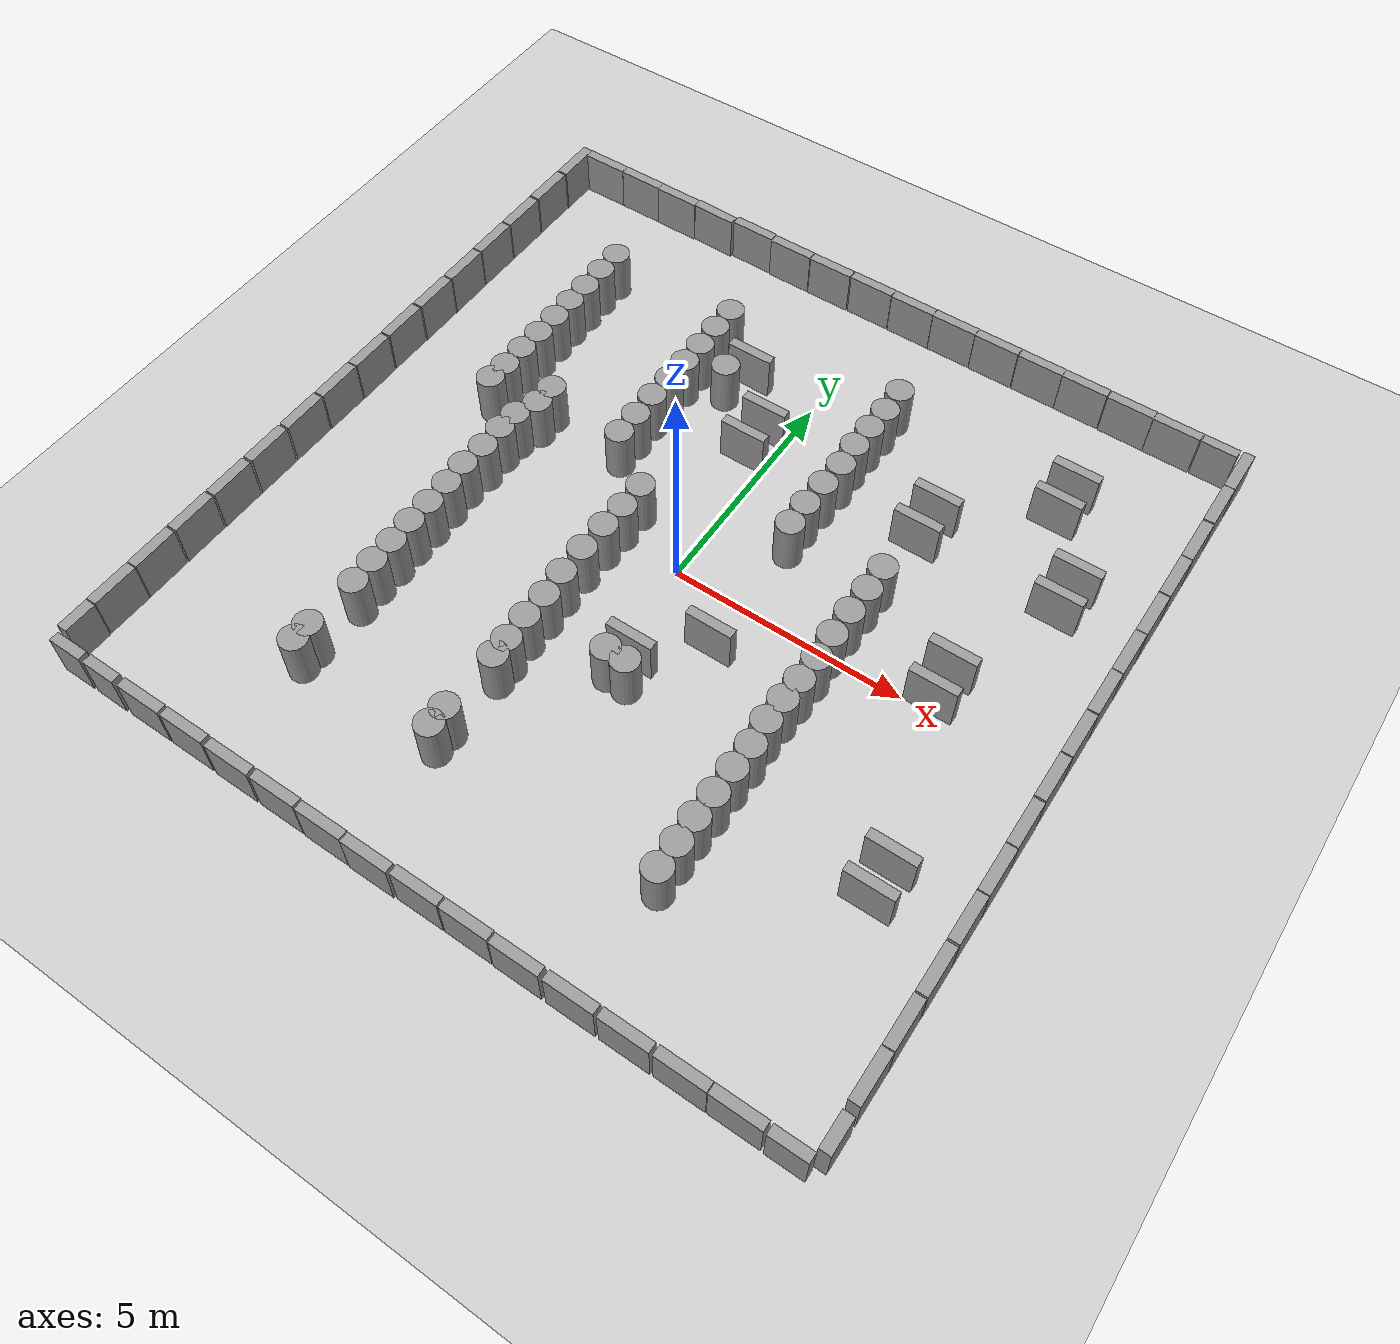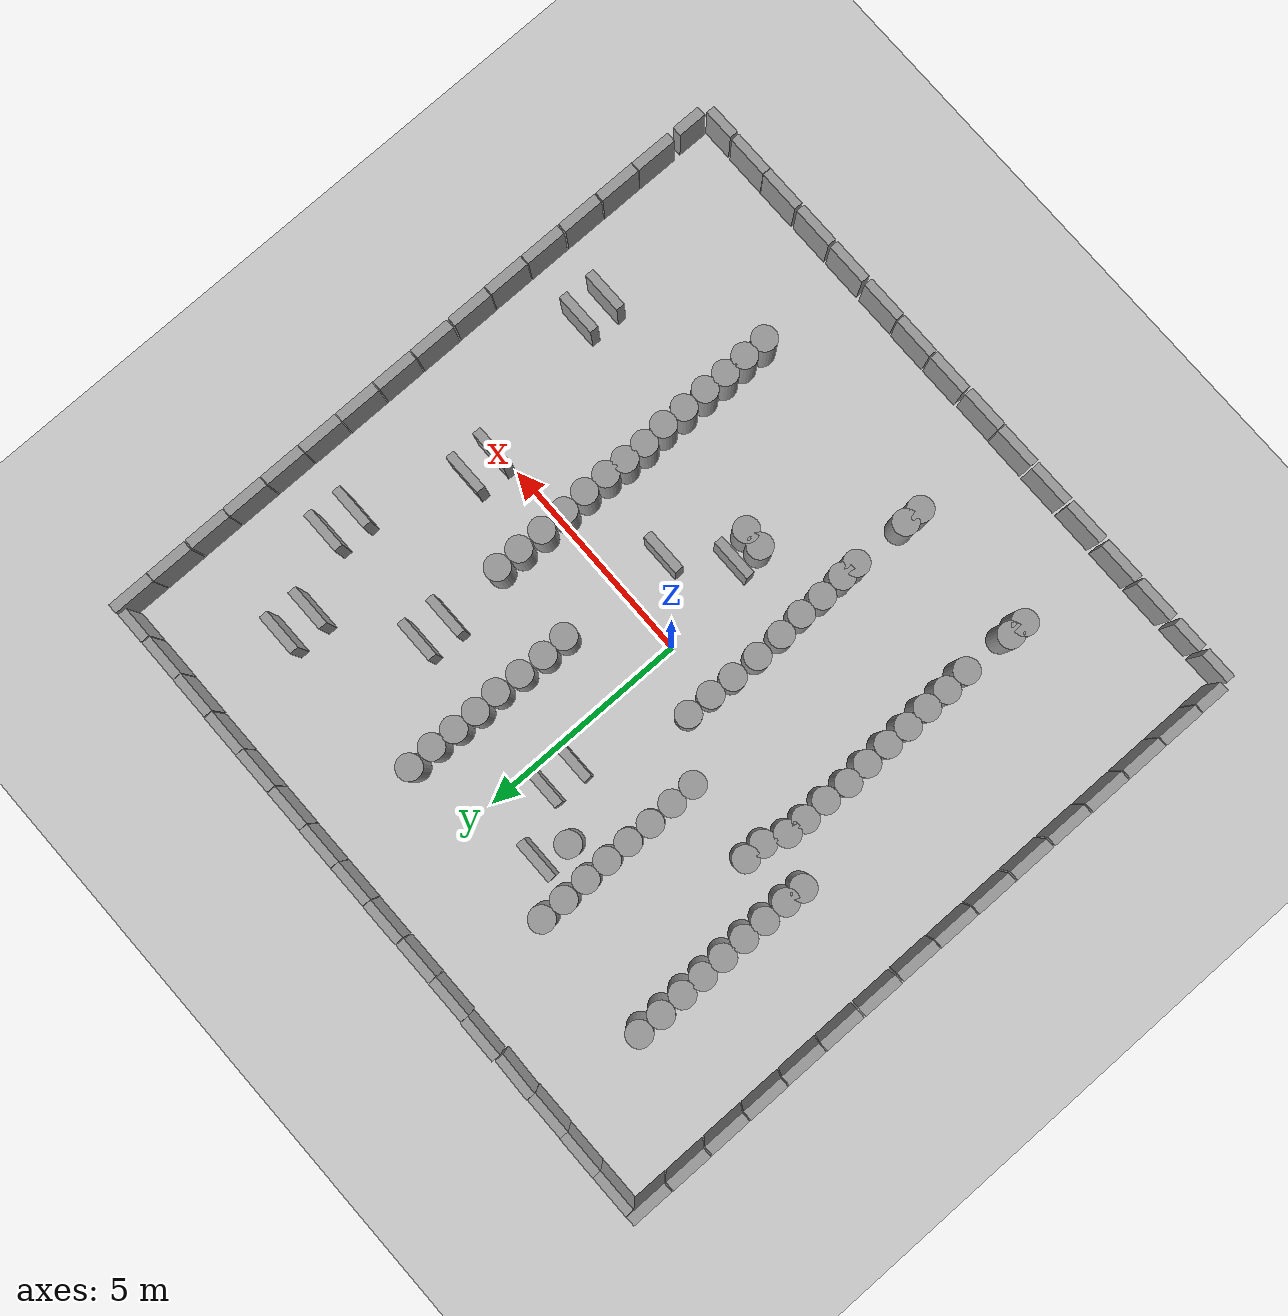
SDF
<sdf version="1.6">
 <world name="default">
  <light name="sun" type="directional">
   <pose>0 0 10 0 -0 0</pose>
   <diffuse>0.8 0.8 0.8 1</diffuse>
   <specular>0.1 0.1 0.1 1</specular>
   <attenuation>
    <range>1000</range>
    <constant>0.9</constant>
    <linear>0.01</linear>
    <quadratic>0.001</quadratic>
   </attenuation>
   <direction>-0.5 0.5 -1</direction>
  </light>
  <model name="ground_plane">
   <static>1</static>
   <static>1</static>
   <link name="link">
    <collision name="collision">
     <geometry><plane><normal>0 0 1</normal><size>100 100</size></plane></geometry>
     <surface><friction><ode><mu>100</mu><mu2>50</mu2></ode></friction></surface>
    </collision>
    <visual name="visual">
     <cast_shadows>0</cast_shadows>
     <geometry><plane><normal>0 0 1</normal><size>100 100</size></plane></geometry>
     <material>
      <script><uri>file://media/materials/scripts/gazebo.material</uri><name>Gazebo/Grey</name></script>
     </material>
    </visual>
   </link>
  </model>
  <gravity>0 0 -9.8</gravity>
  <magnetic_field>6e-06 2.3e-05 -4.2e-05</magnetic_field>
  <atmosphere type="adiabatic"/>
  <physics name="default_physics" default="0" type="ode">
   <max_step_size>0.001</max_step_size>
   <real_time_factor>1</real_time_factor>
   <real_time_update_rate>1000</real_time_update_rate>
  </physics>
  <scene><ambient>0.4 0.4 0.4 1</ambient><background>0.7 0.7 0.7 1</background><shadows>1</shadows></scene>
  <spherical_coordinates>
   <surface_model>EARTH_WGS84</surface_model>
   <latitude_deg>0</latitude_deg>
   <longitude_deg>0</longitude_deg>
   <elevation>0</elevation>
   <heading_deg>0</heading_deg>
  </spherical_coordinates>
  <audio><device>default</device></audio>
  <model name="unit_box_clone">
   <pose>-7.49845 8.11998 0.5 0 -0 0.000212</pose>
   <link name="link">
    <inertial>
     <mass>1</mass>
     <inertia>
      <ixx>0.166667</ixx>
      <ixy>0</ixy>
      <ixz>0</ixz>
      <iyy>0.166667</iyy>
      <iyz>0</iyz>
      <izz>0.166667</izz>
     </inertia>
    </inertial>
    <collision name="collision"><geometry><box><size>1 0.210541 1</size></box></geometry></collision>
    <visual name="visual">
     <geometry><box><size>1 0.210541 1</size></box></geometry>
     <material>
      <script><name>Gazebo/Grey</name><uri>file://media/materials/scripts/gazebo.material</uri></script>
     </material>
    </visual>
   </link>
  </model>
  <model name="unit_box_clone_0">
   <pose>-6.49721 8.1197 0.5 -0 -0 -0.002586</pose>
   <link name="link">
    <inertial>
     <mass>1</mass>
     <inertia>
      <ixx>0.166667</ixx>
      <ixy>0</ixy>
      <ixz>0</ixz>
      <iyy>0.166667</iyy>
      <iyz>0</iyz>
      <izz>0.166667</izz>
     </inertia>
    </inertial>
    <collision name="collision"><geometry><box><size>1 0.210541 1</size></box></geometry></collision>
    <visual name="visual">
     <geometry><box><size>1 0.210541 1</size></box></geometry>
     <material>
      <script><name>Gazebo/Grey</name><uri>file://media/materials/scripts/gazebo.material</uri></script>
     </material>
    </visual>
   </link>
  </model>
  <model name="unit_box_clone_1">
   <pose>-5.49724 8.10823 0.5 0 -0 -0.002585</pose>
   <link name="link">
    <inertial>
     <mass>1</mass>
     <inertia>
      <ixx>0.166667</ixx>
      <ixy>0</ixy>
      <ixz>0</ixz>
      <iyy>0.166667</iyy>
      <iyz>0</iyz>
      <izz>0.166667</izz>
     </inertia>
    </inertial>
    <collision name="collision"><geometry><box><size>1 0.210541 1</size></box></geometry></collision>
    <visual name="visual">
     <geometry><box><size>1 0.210541 1</size></box></geometry>
     <material>
      <script><name>Gazebo/Grey</name><uri>file://media/materials/scripts/gazebo.material</uri></script>
     </material>
    </visual>
   </link>
  </model>
  <model name="unit_box_clone_2">
   <pose>-4.49476 8.11056 0.5 -0 -0 -0.027056</pose>
   <link name="link">
    <inertial>
     <mass>1</mass>
     <inertia>
      <ixx>0.166667</ixx>
      <ixy>0</ixy>
      <ixz>0</ixz>
      <iyy>0.166667</iyy>
      <iyz>0</iyz>
      <izz>0.166667</izz>
     </inertia>
    </inertial>
    <collision name="collision"><geometry><box><size>1 0.210541 1</size></box></geometry></collision>
    <visual name="visual">
     <geometry><box><size>1 0.210541 1</size></box></geometry>
     <material>
      <script><name>Gazebo/Grey</name><uri>file://media/materials/scripts/gazebo.material</uri></script>
     </material>
    </visual>
   </link>
  </model>
  <model name="unit_box_clone_3">
   <pose>-3.46832 8.14916 0.499999 -1e-06 2e-06 -0.008226</pose>
   <link name="link">
    <inertial>
     <mass>1</mass>
     <inertia>
      <ixx>0.166667</ixx>
      <ixy>0</ixy>
      <ixz>0</ixz>
      <iyy>0.166667</iyy>
      <iyz>0</iyz>
      <izz>0.166667</izz>
     </inertia>
    </inertial>
    <collision name="collision"><geometry><box><size>1 0.210541 1</size></box></geometry></collision>
    <visual name="visual">
     <geometry><box><size>1 0.210541 1</size></box></geometry>
     <material>
      <script><name>Gazebo/Grey</name><uri>file://media/materials/scripts/gazebo.material</uri></script>
     </material>
    </visual>
   </link>
  </model>
  <model name="unit_box_clone_4">
   <pose>-2.46316 8.11867 0.5 0 -0 0.000212</pose>
   <link name="link">
    <inertial>
     <mass>1</mass>
     <inertia>
      <ixx>0.166667</ixx>
      <ixy>0</ixy>
      <ixz>0</ixz>
      <iyy>0.166667</iyy>
      <iyz>0</iyz>
      <izz>0.166667</izz>
     </inertia>
    </inertial>
    <collision name="collision"><geometry><box><size>1 0.210541 1</size></box></geometry></collision>
    <visual name="visual">
     <geometry><box><size>1 0.210541 1</size></box></geometry>
     <material>
      <script><name>Gazebo/Grey</name><uri>file://media/materials/scripts/gazebo.material</uri></script>
     </material>
    </visual>
   </link>
  </model>
  <model name="unit_box_clone_5">
   <pose>-1.44425 8.11201 0.5 0 -0 0.000212</pose>
   <link name="link">
    <inertial>
     <mass>1</mass>
     <inertia>
      <ixx>0.166667</ixx>
      <ixy>0</ixy>
      <ixz>0</ixz>
      <iyy>0.166667</iyy>
      <iyz>0</iyz>
      <izz>0.166667</izz>
     </inertia>
    </inertial>
    <collision name="collision"><geometry><box><size>1 0.210541 1</size></box></geometry></collision>
    <visual name="visual">
     <geometry><box><size>1 0.210541 1</size></box></geometry>
     <material>
      <script><name>Gazebo/Grey</name><uri>file://media/materials/scripts/gazebo.material</uri></script>
     </material>
    </visual>
   </link>
  </model>
  <model name="unit_box_clone_6">
   <pose>-0.418678 8.11866 0.5 0 -0 0.000212</pose>
   <link name="link">
    <inertial>
     <mass>1</mass>
     <inertia>
      <ixx>0.166667</ixx>
      <ixy>0</ixy>
      <ixz>0</ixz>
      <iyy>0.166667</iyy>
      <iyz>0</iyz>
      <izz>0.166667</izz>
     </inertia>
    </inertial>
    <collision name="collision"><geometry><box><size>1 0.210541 1</size></box></geometry></collision>
    <visual name="visual">
     <geometry><box><size>1 0.210541 1</size></box></geometry>
     <material>
      <script><name>Gazebo/Grey</name><uri>file://media/materials/scripts/gazebo.material</uri></script>
     </material>
    </visual>
   </link>
  </model>
  <model name="unit_box_clone_7">
   <pose>0.592841 8.11153 0.5 0 -0 0.000212</pose>
   <link name="link">
    <inertial>
     <mass>1</mass>
     <inertia>
      <ixx>0.166667</ixx>
      <ixy>0</ixy>
      <ixz>0</ixz>
      <iyy>0.166667</iyy>
      <iyz>0</iyz>
      <izz>0.166667</izz>
     </inertia>
    </inertial>
    <collision name="collision"><geometry><box><size>1 0.210541 1</size></box></geometry></collision>
    <visual name="visual">
     <geometry><box><size>1 0.210541 1</size></box></geometry>
     <material>
      <script><name>Gazebo/Grey</name><uri>file://media/materials/scripts/gazebo.material</uri></script>
     </material>
    </visual>
   </link>
  </model>
  <model name="unit_box_clone_8">
   <pose>1.60043 8.11004 0.5 0 -0 0.000212</pose>
   <link name="link">
    <inertial>
     <mass>1</mass>
     <inertia>
      <ixx>0.166667</ixx>
      <ixy>0</ixy>
      <ixz>0</ixz>
      <iyy>0.166667</iyy>
      <iyz>0</iyz>
      <izz>0.166667</izz>
     </inertia>
    </inertial>
    <collision name="collision"><geometry><box><size>1 0.210541 1</size></box></geometry></collision>
    <visual name="visual">
     <geometry><box><size>1 0.210541 1</size></box></geometry>
     <material>
      <script><name>Gazebo/Grey</name><uri>file://media/materials/scripts/gazebo.material</uri></script>
     </material>
    </visual>
   </link>
  </model>
  <model name="unit_box_clone_9">
   <pose>2.60987 8.10285 0.5 0 -0 0.000212</pose>
   <link name="link">
    <inertial>
     <mass>1</mass>
     <inertia>
      <ixx>0.166667</ixx>
      <ixy>0</ixy>
      <ixz>0</ixz>
      <iyy>0.166667</iyy>
      <iyz>0</iyz>
      <izz>0.166667</izz>
     </inertia>
    </inertial>
    <collision name="collision"><geometry><box><size>1 0.210541 1</size></box></geometry></collision>
    <visual name="visual">
     <geometry><box><size>1 0.210541 1</size></box></geometry>
     <material>
      <script><name>Gazebo/Grey</name><uri>file://media/materials/scripts/gazebo.material</uri></script>
     </material>
    </visual>
   </link>
  </model>
  <model name="unit_box_clone_10">
   <pose>3.62649 8.09926 0.5 0 -0 0.000212</pose>
   <link name="link">
    <inertial>
     <mass>1</mass>
     <inertia>
      <ixx>0.166667</ixx>
      <ixy>0</ixy>
      <ixz>0</ixz>
      <iyy>0.166667</iyy>
      <iyz>0</iyz>
      <izz>0.166667</izz>
     </inertia>
    </inertial>
    <collision name="collision"><geometry><box><size>1 0.210541 1</size></box></geometry></collision>
    <visual name="visual">
     <geometry><box><size>1 0.210541 1</size></box></geometry>
     <material>
      <script><name>Gazebo/Grey</name><uri>file://media/materials/scripts/gazebo.material</uri></script>
     </material>
    </visual>
   </link>
  </model>
  <model name="unit_box_clone_11">
   <pose>4.6331 8.09534 0.5 -0 -0 -0.002941</pose>
   <link name="link">
    <inertial>
     <mass>1</mass>
     <inertia>
      <ixx>0.166667</ixx>
      <ixy>0</ixy>
      <ixz>0</ixz>
      <iyy>0.166667</iyy>
      <iyz>0</iyz>
      <izz>0.166667</izz>
     </inertia>
    </inertial>
    <collision name="collision"><geometry><box><size>1 0.210541 1</size></box></geometry></collision>
    <visual name="visual">
     <geometry><box><size>1 0.210541 1</size></box></geometry>
     <material>
      <script><name>Gazebo/Grey</name><uri>file://media/materials/scripts/gazebo.material</uri></script>
     </material>
    </visual>
   </link>
  </model>
  <model name="unit_box_0_clone_0">
   <pose>8.11522 6.68459 0.5 -0 -0 -0.000409</pose>
   <link name="link">
    <inertial>
     <mass>1</mass>
     <inertia>
      <ixx>0.166667</ixx>
      <ixy>0</ixy>
      <ixz>0</ixz>
      <iyy>0.166667</iyy>
      <iyz>0</iyz>
      <izz>0.166667</izz>
     </inertia>
    </inertial>
    <collision name="collision"><geometry><box><size>0.230819 1 1</size></box></geometry></collision>
    <visual name="visual">
     <geometry><box><size>0.230819 1 1</size></box></geometry>
     <material>
      <script><name>Gazebo/Grey</name><uri>file://media/materials/scripts/gazebo.material</uri></script>
     </material>
    </visual>
   </link>
  </model>
  <model name="unit_box_0_clone_1">
   <pose>8.11915 5.6517 0.5 0 -0 0.000288</pose>
   <link name="link">
    <inertial>
     <mass>1</mass>
     <inertia>
      <ixx>0.166667</ixx>
      <ixy>0</ixy>
      <ixz>0</ixz>
      <iyy>0.166667</iyy>
      <iyz>0</iyz>
      <izz>0.166667</izz>
     </inertia>
    </inertial>
    <collision name="collision"><geometry><box><size>0.230819 1 1</size></box></geometry></collision>
    <visual name="visual">
     <geometry><box><size>0.230819 1 1</size></box></geometry>
     <material>
      <script><name>Gazebo/Grey</name><uri>file://media/materials/scripts/gazebo.material</uri></script>
     </material>
    </visual>
   </link>
  </model>
  <model name="unit_box_0_clone_2">
   <pose>8.11914 4.64016 0.5 0 -0 0.000304</pose>
   <link name="link">
    <inertial>
     <mass>1</mass>
     <inertia>
      <ixx>0.166667</ixx>
      <ixy>0</ixy>
      <ixz>0</ixz>
      <iyy>0.166667</iyy>
      <iyz>0</iyz>
      <izz>0.166667</izz>
     </inertia>
    </inertial>
    <collision name="collision"><geometry><box><size>0.230819 1 1</size></box></geometry></collision>
    <visual name="visual">
     <geometry><box><size>0.230819 1 1</size></box></geometry>
     <material>
      <script><name>Gazebo/Grey</name><uri>file://media/materials/scripts/gazebo.material</uri></script>
     </material>
    </visual>
   </link>
  </model>
  <model name="unit_box_0_clone_3">
   <pose>8.11914 3.62226 0.5 0 -0 -1.6e-05</pose>
   <link name="link">
    <inertial>
     <mass>1</mass>
     <inertia>
      <ixx>0.166667</ixx>
      <ixy>0</ixy>
      <ixz>0</ixz>
      <iyy>0.166667</iyy>
      <iyz>0</iyz>
      <izz>0.166667</izz>
     </inertia>
    </inertial>
    <collision name="collision"><geometry><box><size>0.230819 1 1</size></box></geometry></collision>
    <visual name="visual">
     <geometry><box><size>0.230819 1 1</size></box></geometry>
     <material>
      <script><name>Gazebo/Grey</name><uri>file://media/materials/scripts/gazebo.material</uri></script>
     </material>
    </visual>
   </link>
  </model>
  <model name="unit_box_0_clone_4">
   <pose>8.11332 2.61062 0.5 0 0 -0.001482</pose>
   <link name="link">
    <inertial>
     <mass>1</mass>
     <inertia>
      <ixx>0.166667</ixx>
      <ixy>0</ixy>
      <ixz>0</ixz>
      <iyy>0.166667</iyy>
      <iyz>0</iyz>
      <izz>0.166667</izz>
     </inertia>
    </inertial>
    <collision name="collision"><geometry><box><size>0.230819 1 1</size></box></geometry></collision>
    <visual name="visual">
     <geometry><box><size>0.230819 1 1</size></box></geometry>
     <material>
      <script><name>Gazebo/Grey</name><uri>file://media/materials/scripts/gazebo.material</uri></script>
     </material>
    </visual>
   </link>
  </model>
  <model name="unit_box_0_clone_5">
   <pose>8.11277 1.59919 0.5 0 -0 -1.6e-05</pose>
   <link name="link">
    <inertial>
     <mass>1</mass>
     <inertia>
      <ixx>0.166667</ixx>
      <ixy>0</ixy>
      <ixz>0</ixz>
      <iyy>0.166667</iyy>
      <iyz>0</iyz>
      <izz>0.166667</izz>
     </inertia>
    </inertial>
    <collision name="collision"><geometry><box><size>0.230819 1 1</size></box></geometry></collision>
    <visual name="visual">
     <geometry><box><size>0.230819 1 1</size></box></geometry>
     <material>
      <script><name>Gazebo/Grey</name><uri>file://media/materials/scripts/gazebo.material</uri></script>
     </material>
    </visual>
   </link>
  </model>
  <model name="unit_box_0_clone_6">
   <pose>8.11277 0.574929 0.5 0 -0 -1.6e-05</pose>
   <link name="link">
    <inertial>
     <mass>1</mass>
     <inertia>
      <ixx>0.166667</ixx>
      <ixy>0</ixy>
      <ixz>0</ixz>
      <iyy>0.166667</iyy>
      <iyz>0</iyz>
      <izz>0.166667</izz>
     </inertia>
    </inertial>
    <collision name="collision"><geometry><box><size>0.230819 1 1</size></box></geometry></collision>
    <visual name="visual">
     <geometry><box><size>0.230819 1 1</size></box></geometry>
     <material>
      <script><name>Gazebo/Grey</name><uri>file://media/materials/scripts/gazebo.material</uri></script>
     </material>
    </visual>
   </link>
  </model>
  <model name="unit_box_0_clone_7">
   <pose>8.11276 -0.449329 0.5 0 -0 -1.6e-05</pose>
   <link name="link">
    <inertial>
     <mass>1</mass>
     <inertia>
      <ixx>0.166667</ixx>
      <ixy>0</ixy>
      <ixz>0</ixz>
      <iyy>0.166667</iyy>
      <iyz>0</iyz>
      <izz>0.166667</izz>
     </inertia>
    </inertial>
    <collision name="collision"><geometry><box><size>0.230819 1 1</size></box></geometry></collision>
    <visual name="visual">
     <geometry><box><size>0.230819 1 1</size></box></geometry>
     <material>
      <script><name>Gazebo/Grey</name><uri>file://media/materials/scripts/gazebo.material</uri></script>
     </material>
    </visual>
   </link>
  </model>
  <model name="unit_box_0_clone_8">
   <pose>8.11912 -1.48631 0.5 0 -0 -1.6e-05</pose>
   <link name="link">
    <inertial>
     <mass>1</mass>
     <inertia>
      <ixx>0.166667</ixx>
      <ixy>0</ixy>
      <ixz>0</ixz>
      <iyy>0.166667</iyy>
      <iyz>0</iyz>
      <izz>0.166667</izz>
     </inertia>
    </inertial>
    <collision name="collision"><geometry><box><size>0.230819 1 1</size></box></geometry></collision>
    <visual name="visual">
     <geometry><box><size>0.230819 1 1</size></box></geometry>
     <material>
      <script><name>Gazebo/Grey</name><uri>file://media/materials/scripts/gazebo.material</uri></script>
     </material>
    </visual>
   </link>
  </model>
  <model name="unit_box_0_clone_9">
   <pose>8.12548 -2.50421 0.5 0 -0 -1.6e-05</pose>
   <link name="link">
    <inertial>
     <mass>1</mass>
     <inertia>
      <ixx>0.166667</ixx>
      <ixy>0</ixy>
      <ixz>0</ixz>
      <iyy>0.166667</iyy>
      <iyz>0</iyz>
      <izz>0.166667</izz>
     </inertia>
    </inertial>
    <collision name="collision"><geometry><box><size>0.230819 1 1</size></box></geometry></collision>
    <visual name="visual">
     <geometry><box><size>0.230819 1 1</size></box></geometry>
     <material>
      <script><name>Gazebo/Grey</name><uri>file://media/materials/scripts/gazebo.material</uri></script>
     </material>
    </visual>
   </link>
  </model>
  <model name="unit_box_0_clone_10">
   <pose>8.12331 -3.52223 0.5 0 -0 -1.6e-05</pose>
   <link name="link">
    <inertial>
     <mass>1</mass>
     <inertia>
      <ixx>0.166667</ixx>
      <ixy>0</ixy>
      <ixz>0</ixz>
      <iyy>0.166667</iyy>
      <iyz>0</iyz>
      <izz>0.166667</izz>
     </inertia>
    </inertial>
    <collision name="collision"><geometry><box><size>0.230819 1 1</size></box></geometry></collision>
    <visual name="visual">
     <geometry><box><size>0.230819 1 1</size></box></geometry>
     <material>
      <script><name>Gazebo/Grey</name><uri>file://media/materials/scripts/gazebo.material</uri></script>
     </material>
    </visual>
   </link>
  </model>
  <model name="unit_box_0_clone_11">
   <pose>8.1233 -4.56316 0.5 0 -0 -1.6e-05</pose>
   <link name="link">
    <inertial>
     <mass>1</mass>
     <inertia>
      <ixx>0.166667</ixx>
      <ixy>0</ixy>
      <ixz>0</ixz>
      <iyy>0.166667</iyy>
      <iyz>0</iyz>
      <izz>0.166667</izz>
     </inertia>
    </inertial>
    <collision name="collision"><geometry><box><size>0.230819 1 1</size></box></geometry></collision>
    <visual name="visual">
     <geometry><box><size>0.230819 1 1</size></box></geometry>
     <material>
      <script><name>Gazebo/Grey</name><uri>file://media/materials/scripts/gazebo.material</uri></script>
     </material>
    </visual>
   </link>
  </model>
  <model name="unit_box_0_clone_12">
   <pose>8.11815 -5.59378 0.5 0 -0 -1.6e-05</pose>
   <link name="link">
    <inertial>
     <mass>1</mass>
     <inertia>
      <ixx>0.166667</ixx>
      <ixy>0</ixy>
      <ixz>0</ixz>
      <iyy>0.166667</iyy>
      <iyz>0</iyz>
      <izz>0.166667</izz>
     </inertia>
    </inertial>
    <collision name="collision"><geometry><box><size>0.230819 1 1</size></box></geometry></collision>
    <visual name="visual">
     <geometry><box><size>0.230819 1 1</size></box></geometry>
     <material>
      <script><name>Gazebo/Grey</name><uri>file://media/materials/scripts/gazebo.material</uri></script>
     </material>
    </visual>
   </link>
  </model>
  <model name="unit_box_0_clone_13">
   <pose>8.11333 -6.60776 0.5 -0 -0 -0.005505</pose>
   <link name="link">
    <inertial>
     <mass>1</mass>
     <inertia>
      <ixx>0.166667</ixx>
      <ixy>0</ixy>
      <ixz>0</ixz>
      <iyy>0.166667</iyy>
      <iyz>0</iyz>
      <izz>0.166667</izz>
     </inertia>
    </inertial>
    <collision name="collision"><geometry><box><size>0.230819 1 1</size></box></geometry></collision>
    <visual name="visual">
     <geometry><box><size>0.230819 1 1</size></box></geometry>
     <material>
      <script><name>Gazebo/Grey</name><uri>file://media/materials/scripts/gazebo.material</uri></script>
     </material>
    </visual>
   </link>
  </model>
  <model name="unit_box_clone_15_clone_0">
   <pose>6.71207 -8.13106 0.5 0 -0 0.000212</pose>
   <link name="link">
    <inertial>
     <mass>1</mass>
     <inertia>
      <ixx>0.166667</ixx>
      <ixy>0</ixy>
      <ixz>0</ixz>
      <iyy>0.166667</iyy>
      <iyz>0</iyz>
      <izz>0.166667</izz>
     </inertia>
    </inertial>
    <collision name="collision"><geometry><box><size>1 0.210541 1</size></box></geometry></collision>
    <visual name="visual">
     <geometry><box><size>1 0.210541 1</size></box></geometry>
     <material>
      <script><name>Gazebo/Grey</name><uri>file://media/materials/scripts/gazebo.material</uri></script>
     </material>
    </visual>
   </link>
  </model>
  <model name="unit_box_clone_15_clone_1">
   <pose>5.69715 -8.13105 0.5 0 -0 0.000212</pose>
   <link name="link">
    <inertial>
     <mass>1</mass>
     <inertia>
      <ixx>0.166667</ixx>
      <ixy>0</ixy>
      <ixz>0</ixz>
      <iyy>0.166667</iyy>
      <iyz>0</iyz>
      <izz>0.166667</izz>
     </inertia>
    </inertial>
    <collision name="collision"><geometry><box><size>1 0.210541 1</size></box></geometry></collision>
    <visual name="visual">
     <geometry><box><size>1 0.210541 1</size></box></geometry>
     <material>
      <script><name>Gazebo/Grey</name><uri>file://media/materials/scripts/gazebo.material</uri></script>
     </material>
    </visual>
   </link>
  </model>
  <model name="unit_box_clone_15_clone_2">
   <pose>4.63881 -8.13723 0.5 0 -0 0.000212</pose>
   <link name="link">
    <inertial>
     <mass>1</mass>
     <inertia>
      <ixx>0.166667</ixx>
      <ixy>0</ixy>
      <ixz>0</ixz>
      <iyy>0.166667</iyy>
      <iyz>0</iyz>
      <izz>0.166667</izz>
     </inertia>
    </inertial>
    <collision name="collision"><geometry><box><size>1 0.210541 1</size></box></geometry></collision>
    <visual name="visual">
     <geometry><box><size>1 0.210541 1</size></box></geometry>
     <material>
      <script><name>Gazebo/Grey</name><uri>file://media/materials/scripts/gazebo.material</uri></script>
     </material>
    </visual>
   </link>
  </model>
  <model name="unit_box_clone_15_clone_3">
   <pose>3.57975 -8.13723 0.5 0 -0 0.000212</pose>
   <link name="link">
    <inertial>
     <mass>1</mass>
     <inertia>
      <ixx>0.166667</ixx>
      <ixy>0</ixy>
      <ixz>0</ixz>
      <iyy>0.166667</iyy>
      <iyz>0</iyz>
      <izz>0.166667</izz>
     </inertia>
    </inertial>
    <collision name="collision"><geometry><box><size>1 0.210541 1</size></box></geometry></collision>
    <visual name="visual">
     <geometry><box><size>1 0.210541 1</size></box></geometry>
     <material>
      <script><name>Gazebo/Grey</name><uri>file://media/materials/scripts/gazebo.material</uri></script>
     </material>
    </visual>
   </link>
  </model>
  <model name="unit_box_clone_15_clone_4">
   <pose>2.49815 -8.13722 0.5 0 -0 0.000212</pose>
   <link name="link">
    <inertial>
     <mass>1</mass>
     <inertia>
      <ixx>0.166667</ixx>
      <ixy>0</ixy>
      <ixz>0</ixz>
      <iyy>0.166667</iyy>
      <iyz>0</iyz>
      <izz>0.166667</izz>
     </inertia>
    </inertial>
    <collision name="collision"><geometry><box><size>1 0.210541 1</size></box></geometry></collision>
    <visual name="visual">
     <geometry><box><size>1 0.210541 1</size></box></geometry>
     <material>
      <script><name>Gazebo/Grey</name><uri>file://media/materials/scripts/gazebo.material</uri></script>
     </material>
    </visual>
   </link>
  </model>
  <model name="unit_box_clone_15_clone_5">
   <pose>1.46162 -8.12595 0.5 0 -0 0.000212</pose>
   <link name="link">
    <inertial>
     <mass>1</mass>
     <inertia>
      <ixx>0.166667</ixx>
      <ixy>0</ixy>
      <ixz>0</ixz>
      <iyy>0.166667</iyy>
      <iyz>0</iyz>
      <izz>0.166667</izz>
     </inertia>
    </inertial>
    <collision name="collision"><geometry><box><size>1 0.210541 1</size></box></geometry></collision>
    <visual name="visual">
     <geometry><box><size>1 0.210541 1</size></box></geometry>
     <material>
      <script><name>Gazebo/Grey</name><uri>file://media/materials/scripts/gazebo.material</uri></script>
     </material>
    </visual>
   </link>
  </model>
  <model name="unit_box_clone_15_clone_6">
   <pose>0.425094 -8.12594 0.5 0 -0 0.000212</pose>
   <link name="link">
    <inertial>
     <mass>1</mass>
     <inertia>
      <ixx>0.166667</ixx>
      <ixy>0</ixy>
      <ixz>0</ixz>
      <iyy>0.166667</iyy>
      <iyz>0</iyz>
      <izz>0.166667</izz>
     </inertia>
    </inertial>
    <collision name="collision"><geometry><box><size>1 0.210541 1</size></box></geometry></collision>
    <visual name="visual">
     <geometry><box><size>1 0.210541 1</size></box></geometry>
     <material>
      <script><name>Gazebo/Grey</name><uri>file://media/materials/scripts/gazebo.material</uri></script>
     </material>
    </visual>
   </link>
  </model>
  <model name="unit_box_clone_15_clone_7">
   <pose>-0.633968 -8.14849 0.5 0 -0 0.000212</pose>
   <link name="link">
    <inertial>
     <mass>1</mass>
     <inertia>
      <ixx>0.166667</ixx>
      <ixy>0</ixy>
      <ixz>0</ixz>
      <iyy>0.166667</iyy>
      <iyz>0</iyz>
      <izz>0.166667</izz>
     </inertia>
    </inertial>
    <collision name="collision"><geometry><box><size>1 0.210541 1</size></box></geometry></collision>
    <visual name="visual">
     <geometry><box><size>1 0.210541 1</size></box></geometry>
     <material>
      <script><name>Gazebo/Grey</name><uri>file://media/materials/scripts/gazebo.material</uri></script>
     </material>
    </visual>
   </link>
  </model>
  <model name="unit_box_clone_15_clone_8">
   <pose>-1.65923 -8.13721 0.5 0 -0 0.000212</pose>
   <link name="link">
    <inertial>
     <mass>1</mass>
     <inertia>
      <ixx>0.166667</ixx>
      <ixy>0</ixy>
      <ixz>0</ixz>
      <iyy>0.166667</iyy>
      <iyz>0</iyz>
      <izz>0.166667</izz>
     </inertia>
    </inertial>
    <collision name="collision"><geometry><box><size>1 0.210541 1</size></box></geometry></collision>
    <visual name="visual">
     <geometry><box><size>1 0.210541 1</size></box></geometry>
     <material>
      <script><name>Gazebo/Grey</name><uri>file://media/materials/scripts/gazebo.material</uri></script>
     </material>
    </visual>
   </link>
  </model>
  <model name="unit_box_clone_15_clone_9">
   <pose>-2.70703 -8.12596 0.5 0 -0 0.000212</pose>
   <link name="link">
    <inertial>
     <mass>1</mass>
     <inertia>
      <ixx>0.166667</ixx>
      <ixy>0</ixy>
      <ixz>0</ixz>
      <iyy>0.166667</iyy>
      <iyz>0</iyz>
      <izz>0.166667</izz>
     </inertia>
    </inertial>
    <collision name="collision"><geometry><box><size>1 0.210541 1</size></box></geometry></collision>
    <visual name="visual">
     <geometry><box><size>1 0.210541 1</size></box></geometry>
     <material>
      <script><name>Gazebo/Grey</name><uri>file://media/materials/scripts/gazebo.material</uri></script>
     </material>
    </visual>
   </link>
  </model>
  <model name="unit_box_clone_15_clone_10">
   <pose>-3.77736 -8.12595 0.5 0 -0 0.000212</pose>
   <link name="link">
    <inertial>
     <mass>1</mass>
     <inertia>
      <ixx>0.166667</ixx>
      <ixy>0</ixy>
      <ixz>0</ixz>
      <iyy>0.166667</iyy>
      <iyz>0</iyz>
      <izz>0.166667</izz>
     </inertia>
    </inertial>
    <collision name="collision"><geometry><box><size>1 0.210541 1</size></box></geometry></collision>
    <visual name="visual">
     <geometry><box><size>1 0.210541 1</size></box></geometry>
     <material>
      <script><name>Gazebo/Grey</name><uri>file://media/materials/scripts/gazebo.material</uri></script>
     </material>
    </visual>
   </link>
  </model>
  <model name="unit_box_clone_15_clone_11">
   <pose>-4.85896 -8.11469 0.5 0 -0 0.000212</pose>
   <link name="link">
    <inertial>
     <mass>1</mass>
     <inertia>
      <ixx>0.166667</ixx>
      <ixy>0</ixy>
      <ixz>0</ixz>
      <iyy>0.166667</iyy>
      <iyz>0</iyz>
      <izz>0.166667</izz>
     </inertia>
    </inertial>
    <collision name="collision"><geometry><box><size>1 0.210541 1</size></box></geometry></collision>
    <visual name="visual">
     <geometry><box><size>1 0.210541 1</size></box></geometry>
     <material>
      <script><name>Gazebo/Grey</name><uri>file://media/materials/scripts/gazebo.material</uri></script>
     </material>
    </visual>
   </link>
  </model>
  <model name="unit_box_clone_15_clone_12">
   <pose>-5.91802 -8.11468 0.5 0 -0 0.000212</pose>
   <link name="link">
    <inertial>
     <mass>1</mass>
     <inertia>
      <ixx>0.166667</ixx>
      <ixy>0</ixy>
      <ixz>0</ixz>
      <iyy>0.166667</iyy>
      <iyz>0</iyz>
      <izz>0.166667</izz>
     </inertia>
    </inertial>
    <collision name="collision"><geometry><box><size>1 0.210541 1</size></box></geometry></collision>
    <visual name="visual">
     <geometry><box><size>1 0.210541 1</size></box></geometry>
     <material>
      <script><name>Gazebo/Grey</name><uri>file://media/materials/scripts/gazebo.material</uri></script>
     </material>
    </visual>
   </link>
  </model>
  <model name="unit_box_0_clone_4_clone">
   <pose>-8.12647 7.71768 0.5 0 -0 -1.6e-05</pose>
   <link name="link">
    <inertial>
     <mass>1</mass>
     <inertia>
      <ixx>0.166667</ixx>
      <ixy>0</ixy>
      <ixz>0</ixz>
      <iyy>0.166667</iyy>
      <iyz>0</iyz>
      <izz>0.166667</izz>
     </inertia>
    </inertial>
    <collision name="collision"><geometry><box><size>0.230819 1 1</size></box></geometry></collision>
    <visual name="visual">
     <geometry><box><size>0.230819 1 1</size></box></geometry>
     <material>
      <script><name>Gazebo/Grey</name><uri>file://media/materials/scripts/gazebo.material</uri></script>
     </material>
    </visual>
   </link>
  </model>
  <model name="unit_box_0_clone_4_clone_0">
   <pose>-8.13281 6.68714 0.5 0 -0 -1.6e-05</pose>
   <link name="link">
    <inertial>
     <mass>1</mass>
     <inertia>
      <ixx>0.166667</ixx>
      <ixy>0</ixy>
      <ixz>0</ixz>
      <iyy>0.166667</iyy>
      <iyz>0</iyz>
      <izz>0.166667</izz>
     </inertia>
    </inertial>
    <collision name="collision"><geometry><box><size>0.230819 1 1</size></box></geometry></collision>
    <visual name="visual">
     <geometry><box><size>0.230819 1 1</size></box></geometry>
     <material>
      <script><name>Gazebo/Grey</name><uri>file://media/materials/scripts/gazebo.material</uri></script>
     </material>
    </visual>
   </link>
  </model>
  <model name="unit_box_0_clone_4_clone_1">
   <pose>-8.12606 5.64722 0.5 0 -0 -1.6e-05</pose>
   <link name="link">
    <inertial>
     <mass>1</mass>
     <inertia>
      <ixx>0.166667</ixx>
      <ixy>0</ixy>
      <ixz>0</ixz>
      <iyy>0.166667</iyy>
      <iyz>0</iyz>
      <izz>0.166667</izz>
     </inertia>
    </inertial>
    <collision name="collision"><geometry><box><size>0.230819 1 1</size></box></geometry></collision>
    <visual name="visual">
     <geometry><box><size>0.230819 1 1</size></box></geometry>
     <material>
      <script><name>Gazebo/Grey</name><uri>file://media/materials/scripts/gazebo.material</uri></script>
     </material>
    </visual>
   </link>
  </model>
  <model name="unit_box_0_clone_4_clone_2">
   <pose>-8.12607 4.6208 0.5 0 -0 -1.6e-05</pose>
   <link name="link">
    <inertial>
     <mass>1</mass>
     <inertia>
      <ixx>0.166667</ixx>
      <ixy>0</ixy>
      <ixz>0</ixz>
      <iyy>0.166667</iyy>
      <iyz>0</iyz>
      <izz>0.166667</izz>
     </inertia>
    </inertial>
    <collision name="collision"><geometry><box><size>0.230819 1 1</size></box></geometry></collision>
    <visual name="visual">
     <geometry><box><size>0.230819 1 1</size></box></geometry>
     <material>
      <script><name>Gazebo/Grey</name><uri>file://media/materials/scripts/gazebo.material</uri></script>
     </material>
    </visual>
   </link>
  </model>
  <model name="unit_box_0_clone_4_clone_3">
   <pose>-8.11932 3.59438 0.5 0 -0 -1.6e-05</pose>
   <link name="link">
    <inertial>
     <mass>1</mass>
     <inertia>
      <ixx>0.166667</ixx>
      <ixy>0</ixy>
      <ixz>0</ixz>
      <iyy>0.166667</iyy>
      <iyz>0</iyz>
      <izz>0.166667</izz>
     </inertia>
    </inertial>
    <collision name="collision"><geometry><box><size>0.230819 1 1</size></box></geometry></collision>
    <visual name="visual">
     <geometry><box><size>0.230819 1 1</size></box></geometry>
     <material>
      <script><name>Gazebo/Grey</name><uri>file://media/materials/scripts/gazebo.material</uri></script>
     </material>
    </visual>
   </link>
  </model>
  <model name="unit_box_0_clone_4_clone_4">
   <pose>-8.11932 2.57472 0.5 0 -0 -1.6e-05</pose>
   <link name="link">
    <inertial>
     <mass>1</mass>
     <inertia>
      <ixx>0.166667</ixx>
      <ixy>0</ixy>
      <ixz>0</ixz>
      <iyy>0.166667</iyy>
      <iyz>0</iyz>
      <izz>0.166667</izz>
     </inertia>
    </inertial>
    <collision name="collision"><geometry><box><size>0.230819 1 1</size></box></geometry></collision>
    <visual name="visual">
     <geometry><box><size>0.230819 1 1</size></box></geometry>
     <material>
      <script><name>Gazebo/Grey</name><uri>file://media/materials/scripts/gazebo.material</uri></script>
     </material>
    </visual>
   </link>
  </model>
  <model name="unit_box_0_clone_4_clone_5">
   <pose>-8.12608 1.54155 0.5 0 -0 -1.6e-05</pose>
   <link name="link">
    <inertial>
     <mass>1</mass>
     <inertia>
      <ixx>0.166667</ixx>
      <ixy>0</ixy>
      <ixz>0</ixz>
      <iyy>0.166667</iyy>
      <iyz>0</iyz>
      <izz>0.166667</izz>
     </inertia>
    </inertial>
    <collision name="collision"><geometry><box><size>0.230819 1 1</size></box></geometry></collision>
    <visual name="visual">
     <geometry><box><size>0.230819 1 1</size></box></geometry>
     <material>
      <script><name>Gazebo/Grey</name><uri>file://media/materials/scripts/gazebo.material</uri></script>
     </material>
    </visual>
   </link>
  </model>
  <model name="unit_box_0_clone_4_clone_6">
   <pose>-8.11933 0.501621 0.5 0 -0 -1.6e-05</pose>
   <link name="link">
    <inertial>
     <mass>1</mass>
     <inertia>
      <ixx>0.166667</ixx>
      <ixy>0</ixy>
      <ixz>0</ixz>
      <iyy>0.166667</iyy>
      <iyz>0</iyz>
      <izz>0.166667</izz>
     </inertia>
    </inertial>
    <collision name="collision"><geometry><box><size>0.230819 1 1</size></box></geometry></collision>
    <visual name="visual">
     <geometry><box><size>0.230819 1 1</size></box></geometry>
     <material>
      <script><name>Gazebo/Grey</name><uri>file://media/materials/scripts/gazebo.material</uri></script>
     </material>
    </visual>
   </link>
  </model>
  <model name="unit_box_0_clone_4_clone_7">
   <pose>-8.12609 -0.518043 0.5 0 -0 -1.6e-05</pose>
   <link name="link">
    <inertial>
     <mass>1</mass>
     <inertia>
      <ixx>0.166667</ixx>
      <ixy>0</ixy>
      <ixz>0</ixz>
      <iyy>0.166667</iyy>
      <iyz>0</iyz>
      <izz>0.166667</izz>
     </inertia>
    </inertial>
    <collision name="collision"><geometry><box><size>0.230819 1 1</size></box></geometry></collision>
    <visual name="visual">
     <geometry><box><size>0.230819 1 1</size></box></geometry>
     <material>
      <script><name>Gazebo/Grey</name><uri>file://media/materials/scripts/gazebo.material</uri></script>
     </material>
    </visual>
   </link>
  </model>
  <model name="unit_box_0_clone_4_clone_8">
   <pose>-8.13284 -1.54446 0.5 0 -0 -1.6e-05</pose>
   <link name="link">
    <inertial>
     <mass>1</mass>
     <inertia>
      <ixx>0.166667</ixx>
      <ixy>0</ixy>
      <ixz>0</ixz>
      <iyy>0.166667</iyy>
      <iyz>0</iyz>
      <izz>0.166667</izz>
     </inertia>
    </inertial>
    <collision name="collision"><geometry><box><size>0.230819 1 1</size></box></geometry></collision>
    <visual name="visual">
     <geometry><box><size>0.230819 1 1</size></box></geometry>
     <material>
      <script><name>Gazebo/Grey</name><uri>file://media/materials/scripts/gazebo.material</uri></script>
     </material>
    </visual>
   </link>
  </model>
  <model name="unit_box_0_clone_4_clone_9">
   <pose>-8.13285 -2.58438 0.5 0 -0 -1.6e-05</pose>
   <link name="link">
    <inertial>
     <mass>1</mass>
     <inertia>
      <ixx>0.166667</ixx>
      <ixy>0</ixy>
      <ixz>0</ixz>
      <iyy>0.166667</iyy>
      <iyz>0</iyz>
      <izz>0.166667</izz>
     </inertia>
    </inertial>
    <collision name="collision"><geometry><box><size>0.230819 1 1</size></box></geometry></collision>
    <visual name="visual">
     <geometry><box><size>0.230819 1 1</size></box></geometry>
     <material>
      <script><name>Gazebo/Grey</name><uri>file://media/materials/scripts/gazebo.material</uri></script>
     </material>
    </visual>
   </link>
  </model>
  <model name="unit_box_0_clone_4_clone_10">
   <pose>-8.13285 -3.6243 0.5 0 -0 -1.6e-05</pose>
   <link name="link">
    <inertial>
     <mass>1</mass>
     <inertia>
      <ixx>0.166667</ixx>
      <ixy>0</ixy>
      <ixz>0</ixz>
      <iyy>0.166667</iyy>
      <iyz>0</iyz>
      <izz>0.166667</izz>
     </inertia>
    </inertial>
    <collision name="collision"><geometry><box><size>0.230819 1 1</size></box></geometry></collision>
    <visual name="visual">
     <geometry><box><size>0.230819 1 1</size></box></geometry>
     <material>
      <script><name>Gazebo/Grey</name><uri>file://media/materials/scripts/gazebo.material</uri></script>
     </material>
    </visual>
   </link>
  </model>
  <model name="unit_box_0_clone_4_clone_11">
   <pose>-8.1396 -4.65747 0.5 0 -0 -1.6e-05</pose>
   <link name="link">
    <inertial>
     <mass>1</mass>
     <inertia>
      <ixx>0.166667</ixx>
      <ixy>0</ixy>
      <ixz>0</ixz>
      <iyy>0.166667</iyy>
      <iyz>0</iyz>
      <izz>0.166667</izz>
     </inertia>
    </inertial>
    <collision name="collision"><geometry><box><size>0.230819 1 1</size></box></geometry></collision>
    <visual name="visual">
     <geometry><box><size>0.230819 1 1</size></box></geometry>
     <material>
      <script><name>Gazebo/Grey</name><uri>file://media/materials/scripts/gazebo.material</uri></script>
     </material>
    </visual>
   </link>
  </model>
  <model name="unit_box_0_clone_4_clone_12">
   <pose>-8.1396 -5.69064 0.5 0 -0 -1.6e-05</pose>
   <link name="link">
    <inertial>
     <mass>1</mass>
     <inertia>
      <ixx>0.166667</ixx>
      <ixy>0</ixy>
      <ixz>0</ixz>
      <iyy>0.166667</iyy>
      <iyz>0</iyz>
      <izz>0.166667</izz>
     </inertia>
    </inertial>
    <collision name="collision"><geometry><box><size>0.230819 1 1</size></box></geometry></collision>
    <visual name="visual">
     <geometry><box><size>0.230819 1 1</size></box></geometry>
     <material>
      <script><name>Gazebo/Grey</name><uri>file://media/materials/scripts/gazebo.material</uri></script>
     </material>
    </visual>
   </link>
  </model>
  <model name="unit_box_0_clone_4_clone_13">
   <pose>-8.14113 -6.70873 0.5 0 -0 -0.009128</pose>
   <link name="link">
    <inertial>
     <mass>1</mass>
     <inertia>
      <ixx>0.166667</ixx>
      <ixy>0</ixy>
      <ixz>0</ixz>
      <iyy>0.166667</iyy>
      <iyz>0</iyz>
      <izz>0.166667</izz>
     </inertia>
    </inertial>
    <collision name="collision"><geometry><box><size>0.230819 1 1</size></box></geometry></collision>
    <visual name="visual">
     <geometry><box><size>0.230819 1 1</size></box></geometry>
     <material>
      <script><name>Gazebo/Grey</name><uri>file://media/materials/scripts/gazebo.material</uri></script>
     </material>
    </visual>
   </link>
  </model>
  <model name="unit_box_0_clone_0_clone">
   <pose>8.11438 7.69322 0.5 0 -0 0.00027</pose>
   <link name="link">
    <inertial>
     <mass>1</mass>
     <inertia>
      <ixx>0.166667</ixx>
      <ixy>0</ixy>
      <ixz>0</ixz>
      <iyy>0.166667</iyy>
      <iyz>0</iyz>
      <izz>0.166667</izz>
     </inertia>
    </inertial>
    <collision name="collision"><geometry><box><size>0.230819 1 1</size></box></geometry></collision>
    <visual name="visual">
     <geometry><box><size>0.230819 1 1</size></box></geometry>
     <material>
      <script><name>Gazebo/Grey</name><uri>file://media/materials/scripts/gazebo.material</uri></script>
     </material>
    </visual>
   </link>
  </model>
  <model name="unit_box_clone_11_clone">
   <pose>5.65439 8.08313 0.5 -0 -0 -0.003132</pose>
   <link name="link">
    <inertial>
     <mass>1</mass>
     <inertia>
      <ixx>0.166667</ixx>
      <ixy>0</ixy>
      <ixz>0</ixz>
      <iyy>0.166667</iyy>
      <iyz>0</iyz>
      <izz>0.166667</izz>
     </inertia>
    </inertial>
    <collision name="collision"><geometry><box><size>1 0.210541 1</size></box></geometry></collision>
    <visual name="visual">
     <geometry><box><size>1 0.210541 1</size></box></geometry>
     <material>
      <script><name>Gazebo/Grey</name><uri>file://media/materials/scripts/gazebo.material</uri></script>
     </material>
    </visual>
   </link>
  </model>
  <model name="unit_box_clone_11_clone_0">
   <pose>6.66439 8.07334 0.5 0 0 -0.002912</pose>
   <link name="link">
    <inertial>
     <mass>1</mass>
     <inertia>
      <ixx>0.166667</ixx>
      <ixy>0</ixy>
      <ixz>0</ixz>
      <iyy>0.166667</iyy>
      <iyz>0</iyz>
      <izz>0.166667</izz>
     </inertia>
    </inertial>
    <collision name="collision"><geometry><box><size>1 0.210541 1</size></box></geometry></collision>
    <visual name="visual">
     <geometry><box><size>1 0.210541 1</size></box></geometry>
     <material>
      <script><name>Gazebo/Grey</name><uri>file://media/materials/scripts/gazebo.material</uri></script>
     </material>
    </visual>
   </link>
  </model>
  <model name="unit_box_clone_11_clone_1_clone">
   <pose>7.56437 8.07322 0.499997 -2e-06 -7e-06 -0.00342</pose>
   <link name="link">
    <inertial>
     <mass>1</mass>
     <inertia>
      <ixx>0.166667</ixx>
      <ixy>0</ixy>
      <ixz>0</ixz>
      <iyy>0.166667</iyy>
      <iyz>0</iyz>
      <izz>0.166667</izz>
     </inertia>
    </inertial>
    <collision name="collision"><geometry><box><size>0.750223 0.210541 1</size></box></geometry></collision>
    <visual name="visual">
     <geometry><box><size>0.750223 0.210541 1</size></box></geometry>
     <material>
      <script><name>Gazebo/Grey</name><uri>file://media/materials/scripts/gazebo.material</uri></script>
     </material>
    </visual>
   </link>
  </model>
  <model name="unit_box_clone_11_clone_1_clone_0">
   <pose>-6.90881 -8.11956 0.499997 -2e-06 -8e-06 -0.004561</pose>
   <link name="link">
    <inertial>
     <mass>1</mass>
     <inertia>
      <ixx>0.166667</ixx>
      <ixy>0</ixy>
      <ixz>0</ixz>
      <iyy>0.166667</iyy>
      <iyz>0</iyz>
      <izz>0.166667</izz>
     </inertia>
    </inertial>
    <collision name="collision"><geometry><box><size>0.750223 0.210541 1</size></box></geometry></collision>
    <visual name="visual">
     <geometry><box><size>0.750223 0.210541 1</size></box></geometry>
     <material>
      <script><name>Gazebo/Grey</name><uri>file://media/materials/scripts/gazebo.material</uri></script>
     </material>
    </visual>
   </link>
  </model>
  <model name="unit_box_0_clone_4_clone_13_clone_clone">
   <pose>-8.13833 -7.5766 0.499997 -7e-06 2e-06 -0.012568</pose>
   <link name="link">
    <inertial>
     <mass>1</mass>
     <inertia>
      <ixx>0.166667</ixx>
      <ixy>0</ixy>
      <ixz>0</ixz>
      <iyy>0.166667</iyy>
      <iyz>0</iyz>
      <izz>0.166667</izz>
     </inertia>
    </inertial>
    <collision name="collision"><geometry><box><size>0.230819 0.700336 1</size></box></geometry></collision>
    <visual name="visual">
     <geometry><box><size>0.230819 0.700336 1</size></box></geometry>
     <material>
      <script><name>Gazebo/Grey</name><uri>file://media/materials/scripts/gazebo.material</uri></script>
     </material>
    </visual>
   </link>
  </model>
  <model name="unit_box_clone_11_clone_1_clone_0_clone">
   <pose>-7.75475 -8.122 0.499997 2e-06 7e-06 0.001038</pose>
   <link name="link">
    <inertial>
     <mass>1</mass>
     <inertia>
      <ixx>0.166667</ixx>
      <ixy>0</ixy>
      <ixz>0</ixz>
      <iyy>0.166667</iyy>
      <iyz>0</iyz>
      <izz>0.166667</izz>
     </inertia>
    </inertial>
    <collision name="collision"><geometry><box><size>0.750223 0.210541 1</size></box></geometry></collision>
    <visual name="visual">
     <geometry><box><size>0.750223 0.210541 1</size></box></geometry>
     <material>
      <script><name>Gazebo/Grey</name><uri>file://media/materials/scripts/gazebo.material</uri></script>
     </material>
    </visual>
   </link>
  </model>
  <model name="unit_box_clone_11_clone_1_clone_2">
   <pose>7.64249 -8.13928 0.5 0 -1e-06 0.003871</pose>
   <link name="link">
    <inertial>
     <mass>1</mass>
     <inertia>
      <ixx>0.166667</ixx>
      <ixy>0</ixy>
      <ixz>0</ixz>
      <iyy>0.166667</iyy>
      <iyz>0</iyz>
      <izz>0.166667</izz>
     </inertia>
    </inertial>
    <collision name="collision"><geometry><box><size>0.750223 0.210541 1</size></box></geometry></collision>
    <visual name="visual">
     <geometry><box><size>0.750223 0.210541 1</size></box></geometry>
     <material>
      <script><name>Gazebo/Grey</name><uri>file://media/materials/scripts/gazebo.material</uri></script>
     </material>
    </visual>
   </link>
  </model>
  <model name="unit_box_0_clone_4_clone_13_clone_clone_clone">
   <pose>8.11857 -7.62155 0.499997 -7e-06 -3e-06 -0.006136</pose>
   <link name="link">
    <inertial>
     <mass>1</mass>
     <inertia>
      <ixx>0.166667</ixx>
      <ixy>0</ixy>
      <ixz>0</ixz>
      <iyy>0.166667</iyy>
      <iyz>0</iyz>
      <izz>0.166667</izz>
     </inertia>
    </inertial>
    <collision name="collision"><geometry><box><size>0.230819 0.700336 1</size></box></geometry></collision>
    <visual name="visual">
     <geometry><box><size>0.230819 0.700336 1</size></box></geometry>
     <material>
      <script><name>Gazebo/Grey</name><uri>file://media/materials/scripts/gazebo.material</uri></script>
     </material>
    </visual>
   </link>
  </model>
  <model name="unit_cylinder_153_clone_clone_5_clone_clone_13_clone_0_clone_29_clone_32_clone_0_clone_4_clone_46_clone_42_clone_clone_clone_4_clone_2_clone">
   <static>1</static>
   <pose>-5.48848 5.67157 0 0 -0 0</pose>
   <link name="link">
    <inertial>
     <mass>1</mass>
     <inertia><ixx>0.145833</ixx><ixy>0</ixy><ixz>0</ixz><iyy>0.145833</iyy><iyz>0</iyz><izz>0.125</izz></inertia>
    </inertial>
    <collision name="collision">
     <geometry><cylinder><radius>0.295479</radius><length>2.18667</length></cylinder></geometry>
    </collision>
    <visual name="visual">
     <geometry><cylinder><radius>0.295479</radius><length>2.18667</length></cylinder></geometry>
     <material>
      <script><name>Gazebo/Grey</name><uri>file://media/materials/scripts/gazebo.material</uri></script>
     </material>
    </visual>
   </link>
  </model>
  <model name="unit_cylinder_153_clone_clone_5_clone_clone_13_clone_0_clone_29_clone_32_clone_0_clone_4_clone_46_clone_42_clone_clone_clone_4_clone_2_clone_0">
   <static>1</static>
   <pose>-5.49081 5.09286 0 0 -0 0</pose>
   <link name="link">
    <inertial>
     <mass>1</mass>
     <inertia><ixx>0.145833</ixx><ixy>0</ixy><ixz>0</ixz><iyy>0.145833</iyy><iyz>0</iyz><izz>0.125</izz></inertia>
    </inertial>
    <collision name="collision">
     <geometry><cylinder><radius>0.295479</radius><length>2.18667</length></cylinder></geometry>
    </collision>
    <visual name="visual">
     <geometry><cylinder><radius>0.295479</radius><length>2.18667</length></cylinder></geometry>
     <material>
      <script><name>Gazebo/Grey</name><uri>file://media/materials/scripts/gazebo.material</uri></script>
     </material>
    </visual>
   </link>
  </model>
  <model name="unit_cylinder_153_clone_clone_5_clone_clone_13_clone_0_clone_29_clone_32_clone_0_clone_4_clone_46_clone_42_clone_clone_clone_4_clone_2_clone_1">
   <static>1</static>
   <pose>-5.47828 4.51643 0 0 -0 0</pose>
   <link name="link">
    <inertial>
     <mass>1</mass>
     <inertia><ixx>0.145833</ixx><ixy>0</ixy><ixz>0</ixz><iyy>0.145833</iyy><iyz>0</iyz><izz>0.125</izz></inertia>
    </inertial>
    <collision name="collision">
     <geometry><cylinder><radius>0.295479</radius><length>2.18667</length></cylinder></geometry>
    </collision>
    <visual name="visual">
     <geometry><cylinder><radius>0.295479</radius><length>2.18667</length></cylinder></geometry>
     <material>
      <script><name>Gazebo/Grey</name><uri>file://media/materials/scripts/gazebo.material</uri></script>
     </material>
    </visual>
   </link>
  </model>
  <model name="unit_cylinder_153_clone_clone_5_clone_clone_13_clone_0_clone_29_clone_32_clone_0_clone_4_clone_46_clone_42_clone_clone_clone_4_clone_2_clone_2">
   <static>1</static>
   <pose>-5.47829 3.96506 0 0 -0 0</pose>
   <link name="link">
    <inertial>
     <mass>1</mass>
     <inertia><ixx>0.145833</ixx><ixy>0</ixy><ixz>0</ixz><iyy>0.145833</iyy><iyz>0</iyz><izz>0.125</izz></inertia>
    </inertial>
    <collision name="collision">
     <geometry><cylinder><radius>0.295479</radius><length>2.18667</length></cylinder></geometry>
    </collision>
    <visual name="visual">
     <geometry><cylinder><radius>0.295479</radius><length>2.18667</length></cylinder></geometry>
     <material>
      <script><name>Gazebo/Grey</name><uri>file://media/materials/scripts/gazebo.material</uri></script>
     </material>
    </visual>
   </link>
  </model>
  <model name="unit_cylinder_153_clone_clone_5_clone_clone_13_clone_0_clone_29_clone_32_clone_0_clone_4_clone_46_clone_42_clone_clone_clone_4_clone_2_clone_3">
   <static>1</static>
   <pose>-5.46576 3.41369 0 0 -0 0</pose>
   <link name="link">
    <inertial>
     <mass>1</mass>
     <inertia><ixx>0.145833</ixx><ixy>0</ixy><ixz>0</ixz><iyy>0.145833</iyy><iyz>0</iyz><izz>0.125</izz></inertia>
    </inertial>
    <collision name="collision">
     <geometry><cylinder><radius>0.295479</radius><length>2.18667</length></cylinder></geometry>
    </collision>
    <visual name="visual">
     <geometry><cylinder><radius>0.295479</radius><length>2.18667</length></cylinder></geometry>
     <material>
      <script><name>Gazebo/Grey</name><uri>file://media/materials/scripts/gazebo.material</uri></script>
     </material>
    </visual>
   </link>
  </model>
  <model name="unit_cylinder_153_clone_clone_5_clone_clone_13_clone_0_clone_29_clone_32_clone_0_clone_4_clone_46_clone_42_clone_clone_clone_4_clone_2_clone_4">
   <static>1</static>
   <pose>-5.46576 2.84979 0 0 -0 0</pose>
   <link name="link">
    <inertial>
     <mass>1</mass>
     <inertia><ixx>0.145833</ixx><ixy>0</ixy><ixz>0</ixz><iyy>0.145833</iyy><iyz>0</iyz><izz>0.125</izz></inertia>
    </inertial>
    <collision name="collision">
     <geometry><cylinder><radius>0.295479</radius><length>2.18667</length></cylinder></geometry>
    </collision>
    <visual name="visual">
     <geometry><cylinder><radius>0.295479</radius><length>2.18667</length></cylinder></geometry>
     <material>
      <script><name>Gazebo/Grey</name><uri>file://media/materials/scripts/gazebo.material</uri></script>
     </material>
    </visual>
   </link>
  </model>
  <model name="unit_cylinder_153_clone_clone_5_clone_clone_13_clone_0_clone_29_clone_32_clone_0_clone_4_clone_46_clone_42_clone_clone_clone_4_clone_2_clone_5">
   <static>1</static>
   <pose>-5.4783 2.29842 0 0 -0 0</pose>
   <link name="link">
    <inertial>
     <mass>1</mass>
     <inertia><ixx>0.145833</ixx><ixy>0</ixy><ixz>0</ixz><iyy>0.145833</iyy><iyz>0</iyz><izz>0.125</izz></inertia>
    </inertial>
    <collision name="collision">
     <geometry><cylinder><radius>0.295479</radius><length>2.18667</length></cylinder></geometry>
    </collision>
    <visual name="visual">
     <geometry><cylinder><radius>0.295479</radius><length>2.18667</length></cylinder></geometry>
     <material>
      <script><name>Gazebo/Grey</name><uri>file://media/materials/scripts/gazebo.material</uri></script>
     </material>
    </visual>
   </link>
  </model>
  <model name="unit_cylinder_153_clone_clone_5_clone_clone_13_clone_0_clone_29_clone_32_clone_0_clone_4_clone_46_clone_42_clone_clone_clone_4_clone_2_clone_6">
   <static>1</static>
   <pose>-5.4783 1.73453 0 0 -0 0</pose>
   <link name="link">
    <inertial>
     <mass>1</mass>
     <inertia><ixx>0.145833</ixx><ixy>0</ixy><ixz>0</ixz><iyy>0.145833</iyy><iyz>0</iyz><izz>0.125</izz></inertia>
    </inertial>
    <collision name="collision">
     <geometry><cylinder><radius>0.295479</radius><length>2.18667</length></cylinder></geometry>
    </collision>
    <visual name="visual">
     <geometry><cylinder><radius>0.295479</radius><length>2.18667</length></cylinder></geometry>
     <material>
      <script><name>Gazebo/Grey</name><uri>file://media/materials/scripts/gazebo.material</uri></script>
     </material>
    </visual>
   </link>
  </model>
  <model name="unit_cylinder_153_clone_clone_5_clone_clone_13_clone_0_clone_29_clone_32_clone_0_clone_4_clone_46_clone_42_clone_clone_clone_4_clone_2_clone_7">
   <static>1</static>
   <pose>-5.50336 1.28341 0 0 -0 0</pose>
   <link name="link">
    <inertial>
     <mass>1</mass>
     <inertia><ixx>0.145833</ixx><ixy>0</ixy><ixz>0</ixz><iyy>0.145833</iyy><iyz>0</iyz><izz>0.125</izz></inertia>
    </inertial>
    <collision name="collision">
     <geometry><cylinder><radius>0.295479</radius><length>2.18667</length></cylinder></geometry>
    </collision>
    <visual name="visual">
     <geometry><cylinder><radius>0.295479</radius><length>2.18667</length></cylinder></geometry>
     <material>
      <script><name>Gazebo/Grey</name><uri>file://media/materials/scripts/gazebo.material</uri></script>
     </material>
    </visual>
   </link>
  </model>
  <model name="unit_cylinder_153_clone_clone_5_clone_clone_13_clone_0_clone_29_clone_32_clone_0_clone_4_clone_46_clone_42_clone_clone_clone_4_clone_2_clone_8">
   <static>1</static>
   <pose>-4.30038 1.77211 0 0 -0 0</pose>
   <link name="link">
    <inertial>
     <mass>1</mass>
     <inertia><ixx>0.145833</ixx><ixy>0</ixy><ixz>0</ixz><iyy>0.145833</iyy><iyz>0</iyz><izz>0.125</izz></inertia>
    </inertial>
    <collision name="collision">
     <geometry><cylinder><radius>0.295479</radius><length>2.18667</length></cylinder></geometry>
    </collision>
    <visual name="visual">
     <geometry><cylinder><radius>0.295479</radius><length>2.18667</length></cylinder></geometry>
     <material>
      <script><name>Gazebo/Grey</name><uri>file://media/materials/scripts/gazebo.material</uri></script>
     </material>
    </visual>
   </link>
  </model>
  <model name="unit_cylinder_153_clone_clone_5_clone_clone_13_clone_0_clone_29_clone_32_clone_0_clone_4_clone_46_clone_42_clone_clone_clone_4_clone_2_clone_9">
   <static>1</static>
   <pose>-4.30038 1.29593 0 0 -0 0</pose>
   <link name="link">
    <inertial>
     <mass>1</mass>
     <inertia><ixx>0.145833</ixx><ixy>0</ixy><ixz>0</ixz><iyy>0.145833</iyy><iyz>0</iyz><izz>0.125</izz></inertia>
    </inertial>
    <collision name="collision">
     <geometry><cylinder><radius>0.295479</radius><length>2.18667</length></cylinder></geometry>
    </collision>
    <visual name="visual">
     <geometry><cylinder><radius>0.295479</radius><length>2.18667</length></cylinder></geometry>
     <material>
      <script><name>Gazebo/Grey</name><uri>file://media/materials/scripts/gazebo.material</uri></script>
     </material>
    </visual>
   </link>
  </model>
  <model name="unit_cylinder_153_clone_clone_5_clone_clone_13_clone_0_clone_29_clone_32_clone_0_clone_4_clone_46_clone_42_clone_clone_clone_4_clone_2_clone_10">
   <static>1</static>
   <pose>-4.47582 0.794688 0 0 -0 0</pose>
   <link name="link">
    <inertial>
     <mass>1</mass>
     <inertia><ixx>0.145833</ixx><ixy>0</ixy><ixz>0</ixz><iyy>0.145833</iyy><iyz>0</iyz><izz>0.125</izz></inertia>
    </inertial>
    <collision name="collision">
     <geometry><cylinder><radius>0.295479</radius><length>2.18667</length></cylinder></geometry>
    </collision>
    <visual name="visual">
     <geometry><cylinder><radius>0.295479</radius><length>2.18667</length></cylinder></geometry>
     <material>
      <script><name>Gazebo/Grey</name><uri>file://media/materials/scripts/gazebo.material</uri></script>
     </material>
    </visual>
   </link>
  </model>
  <model name="unit_cylinder_153_clone_clone_5_clone_clone_13_clone_0_clone_29_clone_32_clone_0_clone_4_clone_46_clone_42_clone_clone_clone_4_clone_2_clone_11">
   <static>1</static>
   <pose>-4.50088 0.331037 0 0 -0 0</pose>
   <link name="link">
    <inertial>
     <mass>1</mass>
     <inertia><ixx>0.145833</ixx><ixy>0</ixy><ixz>0</ixz><iyy>0.145833</iyy><iyz>0</iyz><izz>0.125</izz></inertia>
    </inertial>
    <collision name="collision">
     <geometry><cylinder><radius>0.295479</radius><length>2.18667</length></cylinder></geometry>
    </collision>
    <visual name="visual">
     <geometry><cylinder><radius>0.295479</radius><length>2.18667</length></cylinder></geometry>
     <material>
      <script><name>Gazebo/Grey</name><uri>file://media/materials/scripts/gazebo.material</uri></script>
     </material>
    </visual>
   </link>
  </model>
  <model name="unit_cylinder_153_clone_clone_5_clone_clone_13_clone_0_clone_29_clone_32_clone_0_clone_4_clone_46_clone_42_clone_clone_clone_4_clone_2_clone_12">
   <static>1</static>
   <pose>-4.48835 -0.232862 0 0 -0 0</pose>
   <link name="link">
    <inertial>
     <mass>1</mass>
     <inertia><ixx>0.145833</ixx><ixy>0</ixy><ixz>0</ixz><iyy>0.145833</iyy><iyz>0</iyz><izz>0.125</izz></inertia>
    </inertial>
    <collision name="collision">
     <geometry><cylinder><radius>0.295479</radius><length>2.18667</length></cylinder></geometry>
    </collision>
    <visual name="visual">
     <geometry><cylinder><radius>0.295479</radius><length>2.18667</length></cylinder></geometry>
     <material>
      <script><name>Gazebo/Grey</name><uri>file://media/materials/scripts/gazebo.material</uri></script>
     </material>
    </visual>
   </link>
  </model>
  <model name="unit_cylinder_153_clone_clone_5_clone_clone_13_clone_0_clone_29_clone_32_clone_0_clone_4_clone_46_clone_42_clone_clone_clone_4_clone_2_clone_13">
   <static>1</static>
   <pose>-4.52595 -0.809293 0 0 -0 0</pose>
   <link name="link">
    <inertial>
     <mass>1</mass>
     <inertia><ixx>0.145833</ixx><ixy>0</ixy><ixz>0</ixz><iyy>0.145833</iyy><iyz>0</iyz><izz>0.125</izz></inertia>
    </inertial>
    <collision name="collision">
     <geometry><cylinder><radius>0.295479</radius><length>2.18667</length></cylinder></geometry>
    </collision>
    <visual name="visual">
     <geometry><cylinder><radius>0.295479</radius><length>2.18667</length></cylinder></geometry>
     <material>
      <script><name>Gazebo/Grey</name><uri>file://media/materials/scripts/gazebo.material</uri></script>
     </material>
    </visual>
   </link>
  </model>
  <model name="unit_cylinder_153_clone_clone_5_clone_clone_13_clone_0_clone_29_clone_32_clone_0_clone_4_clone_46_clone_42_clone_clone_clone_4_clone_2_clone_14">
   <static>1</static>
   <pose>-4.48836 -1.36066 0 0 -0 0</pose>
   <link name="link">
    <inertial>
     <mass>1</mass>
     <inertia><ixx>0.145833</ixx><ixy>0</ixy><ixz>0</ixz><iyy>0.145833</iyy><iyz>0</iyz><izz>0.125</izz></inertia>
    </inertial>
    <collision name="collision">
     <geometry><cylinder><radius>0.295479</radius><length>2.18667</length></cylinder></geometry>
    </collision>
    <visual name="visual">
     <geometry><cylinder><radius>0.295479</radius><length>2.18667</length></cylinder></geometry>
     <material>
      <script><name>Gazebo/Grey</name><uri>file://media/materials/scripts/gazebo.material</uri></script>
     </material>
    </visual>
   </link>
  </model>
  <model name="unit_cylinder_153_clone_clone_5_clone_clone_13_clone_0_clone_29_clone_32_clone_0_clone_4_clone_46_clone_42_clone_clone_clone_4_clone_2_clone_15">
   <static>1</static>
   <pose>-4.47583 -1.93709 0 0 -0 0</pose>
   <link name="link">
    <inertial>
     <mass>1</mass>
     <inertia><ixx>0.145833</ixx><ixy>0</ixy><ixz>0</ixz><iyy>0.145833</iyy><iyz>0</iyz><izz>0.125</izz></inertia>
    </inertial>
    <collision name="collision">
     <geometry><cylinder><radius>0.295479</radius><length>2.18667</length></cylinder></geometry>
    </collision>
    <visual name="visual">
     <geometry><cylinder><radius>0.295479</radius><length>2.18667</length></cylinder></geometry>
     <material>
      <script><name>Gazebo/Grey</name><uri>file://media/materials/scripts/gazebo.material</uri></script>
     </material>
    </visual>
   </link>
  </model>
  <model name="unit_cylinder_153_clone_clone_5_clone_clone_13_clone_0_clone_29_clone_32_clone_0_clone_4_clone_46_clone_42_clone_clone_clone_4_clone_2_clone_16">
   <static>1</static>
   <pose>-4.47583 -2.48846 0 0 -0 0</pose>
   <link name="link">
    <inertial>
     <mass>1</mass>
     <inertia><ixx>0.145833</ixx><ixy>0</ixy><ixz>0</ixz><iyy>0.145833</iyy><iyz>0</iyz><izz>0.125</izz></inertia>
    </inertial>
    <collision name="collision">
     <geometry><cylinder><radius>0.295479</radius><length>2.18667</length></cylinder></geometry>
    </collision>
    <visual name="visual">
     <geometry><cylinder><radius>0.295479</radius><length>2.18667</length></cylinder></geometry>
     <material>
      <script><name>Gazebo/Grey</name><uri>file://media/materials/scripts/gazebo.material</uri></script>
     </material>
    </visual>
   </link>
  </model>
  <model name="unit_cylinder_153_clone_clone_5_clone_clone_13_clone_0_clone_29_clone_32_clone_0_clone_4_clone_46_clone_42_clone_clone_clone_4_clone_2_clone_17">
   <static>1</static>
   <pose>-4.45078 -3.03983 0 0 -0 0</pose>
   <link name="link">
    <inertial>
     <mass>1</mass>
     <inertia><ixx>0.145833</ixx><ixy>0</ixy><ixz>0</ixz><iyy>0.145833</iyy><iyz>0</iyz><izz>0.125</izz></inertia>
    </inertial>
    <collision name="collision">
     <geometry><cylinder><radius>0.295479</radius><length>2.18667</length></cylinder></geometry>
    </collision>
    <visual name="visual">
     <geometry><cylinder><radius>0.295479</radius><length>2.18667</length></cylinder></geometry>
     <material>
      <script><name>Gazebo/Grey</name><uri>file://media/materials/scripts/gazebo.material</uri></script>
     </material>
    </visual>
   </link>
  </model>
  <model name="unit_cylinder_153_clone_clone_5_clone_clone_13_clone_0_clone_29_clone_32_clone_0_clone_4_clone_46_clone_42_clone_clone_clone_4_clone_2_clone_18">
   <static>1</static>
   <pose>-4.45078 -3.5912 0 0 -0 0</pose>
   <link name="link">
    <inertial>
     <mass>1</mass>
     <inertia><ixx>0.145833</ixx><ixy>0</ixy><ixz>0</ixz><iyy>0.145833</iyy><iyz>0</iyz><izz>0.125</izz></inertia>
    </inertial>
    <collision name="collision">
     <geometry><cylinder><radius>0.295479</radius><length>2.18667</length></cylinder></geometry>
    </collision>
    <visual name="visual">
     <geometry><cylinder><radius>0.295479</radius><length>2.18667</length></cylinder></geometry>
     <material>
      <script><name>Gazebo/Grey</name><uri>file://media/materials/scripts/gazebo.material</uri></script>
     </material>
    </visual>
   </link>
  </model>
  <model name="unit_cylinder_153_clone_clone_5_clone_clone_13_clone_0_clone_29_clone_32_clone_0_clone_4_clone_46_clone_42_clone_clone_clone_4_clone_2_clone_19">
   <static>1</static>
   <pose>-4.42572 -4.1551 0 0 -0 0</pose>
   <link name="link">
    <inertial>
     <mass>1</mass>
     <inertia><ixx>0.145833</ixx><ixy>0</ixy><ixz>0</ixz><iyy>0.145833</iyy><iyz>0</iyz><izz>0.125</izz></inertia>
    </inertial>
    <collision name="collision">
     <geometry><cylinder><radius>0.295479</radius><length>2.18667</length></cylinder></geometry>
    </collision>
    <visual name="visual">
     <geometry><cylinder><radius>0.295479</radius><length>2.18667</length></cylinder></geometry>
     <material>
      <script><name>Gazebo/Grey</name><uri>file://media/materials/scripts/gazebo.material</uri></script>
     </material>
    </visual>
   </link>
  </model>
  <model name="unit_cylinder_153_clone_clone_5_clone_clone_13_clone_0_clone_29_clone_32_clone_0_clone_4_clone_46_clone_42_clone_clone_clone_4_clone_2_clone_20">
   <static>1</static>
   <pose>-4.47585 -5.33302 0 0 -0 0</pose>
   <link name="link">
    <inertial>
     <mass>1</mass>
     <inertia><ixx>0.145833</ixx><ixy>0</ixy><ixz>0</ixz><iyy>0.145833</iyy><iyz>0</iyz><izz>0.125</izz></inertia>
    </inertial>
    <collision name="collision">
     <geometry><cylinder><radius>0.295479</radius><length>2.18667</length></cylinder></geometry>
    </collision>
    <visual name="visual">
     <geometry><cylinder><radius>0.295479</radius><length>2.18667</length></cylinder></geometry>
     <material>
      <script><name>Gazebo/Grey</name><uri>file://media/materials/scripts/gazebo.material</uri></script>
     </material>
    </visual>
   </link>
  </model>
  <model name="unit_cylinder_153_clone_clone_5_clone_clone_13_clone_0_clone_29_clone_32_clone_0_clone_4_clone_46_clone_42_clone_clone_clone_4_clone_2_clone_21">
   <static>1</static>
   <pose>-4.47585 -5.72148 0 0 -0 0</pose>
   <link name="link">
    <inertial>
     <mass>1</mass>
     <inertia><ixx>0.145833</ixx><ixy>0</ixy><ixz>0</ixz><iyy>0.145833</iyy><iyz>0</iyz><izz>0.125</izz></inertia>
    </inertial>
    <collision name="collision">
     <geometry><cylinder><radius>0.295479</radius><length>2.18667</length></cylinder></geometry>
    </collision>
    <visual name="visual">
     <geometry><cylinder><radius>0.295479</radius><length>2.18667</length></cylinder></geometry>
     <material>
      <script><name>Gazebo/Grey</name><uri>file://media/materials/scripts/gazebo.material</uri></script>
     </material>
    </visual>
   </link>
  </model>
  <model name="unit_cylinder_153_clone_clone_5_clone_clone_13_clone_0_clone_29_clone_32_clone_0_clone_4_clone_46_clone_42_clone_clone_clone_4_clone_2_clone_22">
   <static>1</static>
   <pose>-2.48903 5.65487 0 0 -0 0</pose>
   <link name="link">
    <inertial>
     <mass>1</mass>
     <inertia><ixx>0.145833</ixx><ixy>0</ixy><ixz>0</ixz><iyy>0.145833</iyy><iyz>0</iyz><izz>0.125</izz></inertia>
    </inertial>
    <collision name="collision">
     <geometry><cylinder><radius>0.295479</radius><length>2.18667</length></cylinder></geometry>
    </collision>
    <visual name="visual">
     <geometry><cylinder><radius>0.295479</radius><length>2.18667</length></cylinder></geometry>
     <material>
      <script><name>Gazebo/Grey</name><uri>file://media/materials/scripts/gazebo.material</uri></script>
     </material>
    </visual>
   </link>
  </model>
  <model name="unit_cylinder_153_clone_clone_5_clone_clone_13_clone_0_clone_29_clone_32_clone_0_clone_4_clone_46_clone_42_clone_clone_clone_4_clone_2_clone_23">
   <static>1</static>
   <pose>-2.48903 5.0711 0 0 -0 0</pose>
   <link name="link">
    <inertial>
     <mass>1</mass>
     <inertia><ixx>0.145833</ixx><ixy>0</ixy><ixz>0</ixz><iyy>0.145833</iyy><iyz>0</iyz><izz>0.125</izz></inertia>
    </inertial>
    <collision name="collision">
     <geometry><cylinder><radius>0.295479</radius><length>2.18667</length></cylinder></geometry>
    </collision>
    <visual name="visual">
     <geometry><cylinder><radius>0.295479</radius><length>2.18667</length></cylinder></geometry>
     <material>
      <script><name>Gazebo/Grey</name><uri>file://media/materials/scripts/gazebo.material</uri></script>
     </material>
    </visual>
   </link>
  </model>
  <model name="unit_cylinder_153_clone_clone_5_clone_clone_13_clone_0_clone_29_clone_32_clone_0_clone_4_clone_46_clone_42_clone_clone_clone_4_clone_2_clone_24">
   <static>1</static>
   <pose>-2.47235 4.47066 0 0 -0 0</pose>
   <link name="link">
    <inertial>
     <mass>1</mass>
     <inertia><ixx>0.145833</ixx><ixy>0</ixy><ixz>0</ixz><iyy>0.145833</iyy><iyz>0</iyz><izz>0.125</izz></inertia>
    </inertial>
    <collision name="collision">
     <geometry><cylinder><radius>0.295479</radius><length>2.18667</length></cylinder></geometry>
    </collision>
    <visual name="visual">
     <geometry><cylinder><radius>0.295479</radius><length>2.18667</length></cylinder></geometry>
     <material>
      <script><name>Gazebo/Grey</name><uri>file://media/materials/scripts/gazebo.material</uri></script>
     </material>
    </visual>
   </link>
  </model>
  <model name="unit_cylinder_153_clone_clone_5_clone_clone_13_clone_0_clone_29_clone_32_clone_0_clone_4_clone_46_clone_42_clone_clone_clone_4_clone_2_clone_25">
   <static>1</static>
   <pose>-2.47236 3.90358 0 0 -0 0</pose>
   <link name="link">
    <inertial>
     <mass>1</mass>
     <inertia><ixx>0.145833</ixx><ixy>0</ixy><ixz>0</ixz><iyy>0.145833</iyy><iyz>0</iyz><izz>0.125</izz></inertia>
    </inertial>
    <collision name="collision">
     <geometry><cylinder><radius>0.295479</radius><length>2.18667</length></cylinder></geometry>
    </collision>
    <visual name="visual">
     <geometry><cylinder><radius>0.295479</radius><length>2.18667</length></cylinder></geometry>
     <material>
      <script><name>Gazebo/Grey</name><uri>file://media/materials/scripts/gazebo.material</uri></script>
     </material>
    </visual>
   </link>
  </model>
  <model name="unit_cylinder_153_clone_clone_5_clone_clone_13_clone_0_clone_29_clone_32_clone_0_clone_4_clone_46_clone_42_clone_clone_clone_4_clone_2_clone_26">
   <static>1</static>
   <pose>-2.47236 3.3365 0 0 -0 0</pose>
   <link name="link">
    <inertial>
     <mass>1</mass>
     <inertia><ixx>0.145833</ixx><ixy>0</ixy><ixz>0</ixz><iyy>0.145833</iyy><iyz>0</iyz><izz>0.125</izz></inertia>
    </inertial>
    <collision name="collision">
     <geometry><cylinder><radius>0.295479</radius><length>2.18667</length></cylinder></geometry>
    </collision>
    <visual name="visual">
     <geometry><cylinder><radius>0.295479</radius><length>2.18667</length></cylinder></geometry>
     <material>
      <script><name>Gazebo/Grey</name><uri>file://media/materials/scripts/gazebo.material</uri></script>
     </material>
    </visual>
   </link>
  </model>
  <model name="unit_cylinder_153_clone_clone_5_clone_clone_13_clone_0_clone_29_clone_32_clone_0_clone_4_clone_46_clone_42_clone_clone_clone_4_clone_2_clone_27">
   <static>1</static>
   <pose>-2.48904 2.75274 0 0 -0 0</pose>
   <link name="link">
    <inertial>
     <mass>1</mass>
     <inertia><ixx>0.145833</ixx><ixy>0</ixy><ixz>0</ixz><iyy>0.145833</iyy><iyz>0</iyz><izz>0.125</izz></inertia>
    </inertial>
    <collision name="collision">
     <geometry><cylinder><radius>0.295479</radius><length>2.18667</length></cylinder></geometry>
    </collision>
    <visual name="visual">
     <geometry><cylinder><radius>0.295479</radius><length>2.18667</length></cylinder></geometry>
     <material>
      <script><name>Gazebo/Grey</name><uri>file://media/materials/scripts/gazebo.material</uri></script>
     </material>
    </visual>
   </link>
  </model>
  <model name="unit_cylinder_153_clone_clone_5_clone_clone_13_clone_0_clone_29_clone_32_clone_0_clone_4_clone_46_clone_42_clone_clone_clone_4_clone_2_clone_28">
   <static>1</static>
   <pose>-2.47237 2.1523 0 0 -0 0</pose>
   <link name="link">
    <inertial>
     <mass>1</mass>
     <inertia><ixx>0.145833</ixx><ixy>0</ixy><ixz>0</ixz><iyy>0.145833</iyy><iyz>0</iyz><izz>0.125</izz></inertia>
    </inertial>
    <collision name="collision">
     <geometry><cylinder><radius>0.295479</radius><length>2.18667</length></cylinder></geometry>
    </collision>
    <visual name="visual">
     <geometry><cylinder><radius>0.295479</radius><length>2.18667</length></cylinder></geometry>
     <material>
      <script><name>Gazebo/Grey</name><uri>file://media/materials/scripts/gazebo.material</uri></script>
     </material>
    </visual>
   </link>
  </model>
  <model name="unit_cylinder_153_clone_clone_5_clone_clone_13_clone_0_clone_29_clone_32_clone_0_clone_4_clone_46_clone_42_clone_clone_clone_4_clone_2_clone_29">
   <static>1</static>
   <pose>-2.47237 1.58522 0 0 -0 0</pose>
   <link name="link">
    <inertial>
     <mass>1</mass>
     <inertia><ixx>0.145833</ixx><ixy>0</ixy><ixz>0</ixz><iyy>0.145833</iyy><iyz>0</iyz><izz>0.125</izz></inertia>
    </inertial>
    <collision name="collision">
     <geometry><cylinder><radius>0.295479</radius><length>2.18667</length></cylinder></geometry>
    </collision>
    <visual name="visual">
     <geometry><cylinder><radius>0.295479</radius><length>2.18667</length></cylinder></geometry>
     <material>
      <script><name>Gazebo/Grey</name><uri>file://media/materials/scripts/gazebo.material</uri></script>
     </material>
    </visual>
   </link>
  </model>
  <model name="unit_cylinder_153_clone_clone_5_clone_clone_13_clone_0_clone_29_clone_32_clone_0_clone_4_clone_46_clone_42_clone_clone_clone_4_clone_2_clone_29_clone">
   <static>1</static>
   <pose>-1.33788 0.711735 0 0 -0 0</pose>
   <link name="link">
    <inertial>
     <mass>1</mass>
     <inertia><ixx>0.145833</ixx><ixy>0</ixy><ixz>0</ixz><iyy>0.145833</iyy><iyz>0</iyz><izz>0.125</izz></inertia>
    </inertial>
    <collision name="collision">
     <geometry><cylinder><radius>0.295479</radius><length>2.18667</length></cylinder></geometry>
    </collision>
    <visual name="visual">
     <geometry><cylinder><radius>0.295479</radius><length>2.18667</length></cylinder></geometry>
     <material>
      <script><name>Gazebo/Grey</name><uri>file://media/materials/scripts/gazebo.material</uri></script>
     </material>
    </visual>
   </link>
  </model>
  <model name="unit_cylinder_153_clone_clone_5_clone_clone_13_clone_0_clone_29_clone_32_clone_0_clone_4_clone_46_clone_42_clone_clone_clone_4_clone_2_clone_29_clone_0">
   <static>1</static>
   <pose>-1.33788 0.103789 0 0 -0 0</pose>
   <link name="link">
    <inertial>
     <mass>1</mass>
     <inertia><ixx>0.145833</ixx><ixy>0</ixy><ixz>0</ixz><iyy>0.145833</iyy><iyz>0</iyz><izz>0.125</izz></inertia>
    </inertial>
    <collision name="collision">
     <geometry><cylinder><radius>0.295479</radius><length>2.18667</length></cylinder></geometry>
    </collision>
    <visual name="visual">
     <geometry><cylinder><radius>0.295479</radius><length>2.18667</length></cylinder></geometry>
     <material>
      <script><name>Gazebo/Grey</name><uri>file://media/materials/scripts/gazebo.material</uri></script>
     </material>
    </visual>
   </link>
  </model>
  <model name="unit_cylinder_153_clone_clone_5_clone_clone_13_clone_0_clone_29_clone_32_clone_0_clone_4_clone_46_clone_42_clone_clone_clone_4_clone_2_clone_29_clone_1">
   <static>1</static>
   <pose>-1.3649 -0.477136 0 0 -0 0</pose>
   <link name="link">
    <inertial>
     <mass>1</mass>
     <inertia><ixx>0.145833</ixx><ixy>0</ixy><ixz>0</ixz><iyy>0.145833</iyy><iyz>0</iyz><izz>0.125</izz></inertia>
    </inertial>
    <collision name="collision">
     <geometry><cylinder><radius>0.295479</radius><length>2.18667</length></cylinder></geometry>
    </collision>
    <visual name="visual">
     <geometry><cylinder><radius>0.295479</radius><length>2.18667</length></cylinder></geometry>
     <material>
      <script><name>Gazebo/Grey</name><uri>file://media/materials/scripts/gazebo.material</uri></script>
     </material>
    </visual>
   </link>
  </model>
  <model name="unit_cylinder_153_clone_clone_5_clone_clone_13_clone_0_clone_29_clone_32_clone_0_clone_4_clone_46_clone_42_clone_clone_clone_4_clone_2_clone_29_clone_2">
   <static>1</static>
   <pose>-1.37842 -1.13912 0 0 -0 0</pose>
   <link name="link">
    <inertial>
     <mass>1</mass>
     <inertia><ixx>0.145833</ixx><ixy>0</ixy><ixz>0</ixz><iyy>0.145833</iyy><iyz>0</iyz><izz>0.125</izz></inertia>
    </inertial>
    <collision name="collision">
     <geometry><cylinder><radius>0.295479</radius><length>2.18667</length></cylinder></geometry>
    </collision>
    <visual name="visual">
     <geometry><cylinder><radius>0.295479</radius><length>2.18667</length></cylinder></geometry>
     <material>
      <script><name>Gazebo/Grey</name><uri>file://media/materials/scripts/gazebo.material</uri></script>
     </material>
    </visual>
   </link>
  </model>
  <model name="unit_cylinder_153_clone_clone_5_clone_clone_13_clone_0_clone_29_clone_32_clone_0_clone_4_clone_46_clone_42_clone_clone_clone_4_clone_2_clone_29_clone_3">
   <static>1</static>
   <pose>-1.36491 -1.80111 0 0 -0 0</pose>
   <link name="link">
    <inertial>
     <mass>1</mass>
     <inertia><ixx>0.145833</ixx><ixy>0</ixy><ixz>0</ixz><iyy>0.145833</iyy><iyz>0</iyz><izz>0.125</izz></inertia>
    </inertial>
    <collision name="collision">
     <geometry><cylinder><radius>0.295479</radius><length>2.18667</length></cylinder></geometry>
    </collision>
    <visual name="visual">
     <geometry><cylinder><radius>0.295479</radius><length>2.18667</length></cylinder></geometry>
     <material>
      <script><name>Gazebo/Grey</name><uri>file://media/materials/scripts/gazebo.material</uri></script>
     </material>
    </visual>
   </link>
  </model>
  <model name="unit_cylinder_153_clone_clone_5_clone_clone_13_clone_0_clone_29_clone_32_clone_0_clone_4_clone_46_clone_42_clone_clone_clone_4_clone_2_clone_29_clone_4">
   <static>1</static>
   <pose>-1.31809 -2.38905 0 0 -0 0</pose>
   <link name="link">
    <inertial>
     <mass>1</mass>
     <inertia><ixx>0.145833</ixx><ixy>0</ixy><ixz>0</ixz><iyy>0.145833</iyy><iyz>0</iyz><izz>0.125</izz></inertia>
    </inertial>
    <collision name="collision">
     <geometry><cylinder><radius>0.295479</radius><length>2.18667</length></cylinder></geometry>
    </collision>
    <visual name="visual">
     <geometry><cylinder><radius>0.295479</radius><length>2.18667</length></cylinder></geometry>
     <material>
      <script><name>Gazebo/Grey</name><uri>file://media/materials/scripts/gazebo.material</uri></script>
     </material>
    </visual>
   </link>
  </model>
  <model name="unit_cylinder_153_clone_clone_5_clone_clone_13_clone_0_clone_29_clone_32_clone_0_clone_4_clone_46_clone_42_clone_clone_clone_4_clone_2_clone_29_clone_5">
   <static>1</static>
   <pose>-1.32696 -2.9652 0 0 -0 0</pose>
   <link name="link">
    <inertial>
     <mass>1</mass>
     <inertia><ixx>0.145833</ixx><ixy>0</ixy><ixz>0</ixz><iyy>0.145833</iyy><iyz>0</iyz><izz>0.125</izz></inertia>
    </inertial>
    <collision name="collision">
     <geometry><cylinder><radius>0.295479</radius><length>2.18667</length></cylinder></geometry>
    </collision>
    <visual name="visual">
     <geometry><cylinder><radius>0.295479</radius><length>2.18667</length></cylinder></geometry>
     <material>
      <script><name>Gazebo/Grey</name><uri>file://media/materials/scripts/gazebo.material</uri></script>
     </material>
    </visual>
   </link>
  </model>
  <model name="unit_cylinder_153_clone_clone_5_clone_clone_13_clone_0_clone_29_clone_32_clone_0_clone_4_clone_46_clone_42_clone_clone_clone_4_clone_2_clone_29_clone_6">
   <static>1</static>
   <pose>-1.2915 -3.55022 0 0 -0 0</pose>
   <link name="link">
    <inertial>
     <mass>1</mass>
     <inertia><ixx>0.145833</ixx><ixy>0</ixy><ixz>0</ixz><iyy>0.145833</iyy><iyz>0</iyz><izz>0.125</izz></inertia>
    </inertial>
    <collision name="collision">
     <geometry><cylinder><radius>0.295479</radius><length>2.18667</length></cylinder></geometry>
    </collision>
    <visual name="visual">
     <geometry><cylinder><radius>0.295479</radius><length>2.18667</length></cylinder></geometry>
     <material>
      <script><name>Gazebo/Grey</name><uri>file://media/materials/scripts/gazebo.material</uri></script>
     </material>
    </visual>
   </link>
  </model>
  <model name="unit_cylinder_153_clone_clone_5_clone_clone_13_clone_0_clone_29_clone_32_clone_0_clone_4_clone_46_clone_42_clone_clone_clone_4_clone_2_clone_29_clone_7">
   <static>1</static>
   <pose>-1.28264 -3.94909 0 0 -0 0</pose>
   <link name="link">
    <inertial>
     <mass>1</mass>
     <inertia><ixx>0.145833</ixx><ixy>0</ixy><ixz>0</ixz><iyy>0.145833</iyy><iyz>0</iyz><izz>0.125</izz></inertia>
    </inertial>
    <collision name="collision">
     <geometry><cylinder><radius>0.295479</radius><length>2.18667</length></cylinder></geometry>
    </collision>
    <visual name="visual">
     <geometry><cylinder><radius>0.295479</radius><length>2.18667</length></cylinder></geometry>
     <material>
      <script><name>Gazebo/Grey</name><uri>file://media/materials/scripts/gazebo.material</uri></script>
     </material>
    </visual>
   </link>
  </model>
  <model name="unit_cylinder_153_clone_clone_5_clone_clone_13_clone_0_clone_29_clone_32_clone_0_clone_4_clone_46_clone_42_clone_clone_clone_4_clone_2_clone_29_clone_8">
   <static>1</static>
   <pose>-1.3181 -5.27867 0 0 -0 0</pose>
   <link name="link">
    <inertial>
     <mass>1</mass>
     <inertia><ixx>0.145833</ixx><ixy>0</ixy><ixz>0</ixz><iyy>0.145833</iyy><iyz>0</iyz><izz>0.125</izz></inertia>
    </inertial>
    <collision name="collision">
     <geometry><cylinder><radius>0.295479</radius><length>2.18667</length></cylinder></geometry>
    </collision>
    <visual name="visual">
     <geometry><cylinder><radius>0.295479</radius><length>2.18667</length></cylinder></geometry>
     <material>
      <script><name>Gazebo/Grey</name><uri>file://media/materials/scripts/gazebo.material</uri></script>
     </material>
    </visual>
   </link>
  </model>
  <model name="unit_cylinder_153_clone_clone_5_clone_clone_13_clone_0_clone_29_clone_32_clone_0_clone_4_clone_46_clone_42_clone_clone_clone_4_clone_2_clone_29_clone_9">
   <static>1</static>
   <pose>-1.31811 -5.69527 0 0 -0 0</pose>
   <link name="link">
    <inertial>
     <mass>1</mass>
     <inertia><ixx>0.145833</ixx><ixy>0</ixy><ixz>0</ixz><iyy>0.145833</iyy><iyz>0</iyz><izz>0.125</izz></inertia>
    </inertial>
    <collision name="collision">
     <geometry><cylinder><radius>0.295479</radius><length>2.18667</length></cylinder></geometry>
    </collision>
    <visual name="visual">
     <geometry><cylinder><radius>0.295479</radius><length>2.18667</length></cylinder></geometry>
     <material>
      <script><name>Gazebo/Grey</name><uri>file://media/materials/scripts/gazebo.material</uri></script>
     </material>
    </visual>
   </link>
  </model>
  <model name="unit_cylinder_153_clone_clone_5_clone_clone_13_clone_0_clone_29_clone_32_clone_0_clone_4_clone_46_clone_42_clone_clone_clone_4_clone_2_clone_29_clone_10">
   <static>1</static>
   <pose>1.60145 5.68902 0 0 -0 0</pose>
   <link name="link">
    <inertial>
     <mass>1</mass>
     <inertia><ixx>0.145833</ixx><ixy>0</ixy><ixz>0</ixz><iyy>0.145833</iyy><iyz>0</iyz><izz>0.125</izz></inertia>
    </inertial>
    <collision name="collision">
     <geometry><cylinder><radius>0.295479</radius><length>2.18667</length></cylinder></geometry>
    </collision>
    <visual name="visual">
     <geometry><cylinder><radius>0.295479</radius><length>2.18667</length></cylinder></geometry>
     <material>
      <script><name>Gazebo/Grey</name><uri>file://media/materials/scripts/gazebo.material</uri></script>
     </material>
    </visual>
   </link>
  </model>
  <model name="unit_cylinder_153_clone_clone_5_clone_clone_13_clone_0_clone_29_clone_32_clone_0_clone_4_clone_46_clone_42_clone_clone_clone_4_clone_2_clone_29_clone_11">
   <static>1</static>
   <pose>1.61502 5.07811 0 0 -0 0</pose>
   <link name="link">
    <inertial>
     <mass>1</mass>
     <inertia><ixx>0.145833</ixx><ixy>0</ixy><ixz>0</ixz><iyy>0.145833</iyy><iyz>0</iyz><izz>0.125</izz></inertia>
    </inertial>
    <collision name="collision">
     <geometry><cylinder><radius>0.295479</radius><length>2.18667</length></cylinder></geometry>
    </collision>
    <visual name="visual">
     <geometry><cylinder><radius>0.295479</radius><length>2.18667</length></cylinder></geometry>
     <material>
      <script><name>Gazebo/Grey</name><uri>file://media/materials/scripts/gazebo.material</uri></script>
     </material>
    </visual>
   </link>
  </model>
  <model name="unit_cylinder_153_clone_clone_5_clone_clone_13_clone_0_clone_29_clone_32_clone_0_clone_4_clone_46_clone_42_clone_clone_clone_4_clone_2_clone_29_clone_12">
   <static>1</static>
   <pose>1.58787 4.50793 0 0 -0 0</pose>
   <link name="link">
    <inertial>
     <mass>1</mass>
     <inertia><ixx>0.145833</ixx><ixy>0</ixy><ixz>0</ixz><iyy>0.145833</iyy><iyz>0</iyz><izz>0.125</izz></inertia>
    </inertial>
    <collision name="collision">
     <geometry><cylinder><radius>0.295479</radius><length>2.18667</length></cylinder></geometry>
    </collision>
    <visual name="visual">
     <geometry><cylinder><radius>0.295479</radius><length>2.18667</length></cylinder></geometry>
     <material>
      <script><name>Gazebo/Grey</name><uri>file://media/materials/scripts/gazebo.material</uri></script>
     </material>
    </visual>
   </link>
  </model>
  <model name="unit_cylinder_153_clone_clone_5_clone_clone_13_clone_0_clone_29_clone_32_clone_0_clone_4_clone_46_clone_42_clone_clone_clone_4_clone_2_clone_29_clone_13">
   <static>1</static>
   <pose>1.57429 3.93776 0 0 -0 0</pose>
   <link name="link">
    <inertial>
     <mass>1</mass>
     <inertia><ixx>0.145833</ixx><ixy>0</ixy><ixz>0</ixz><iyy>0.145833</iyy><iyz>0</iyz><izz>0.125</izz></inertia>
    </inertial>
    <collision name="collision">
     <geometry><cylinder><radius>0.295479</radius><length>2.18667</length></cylinder></geometry>
    </collision>
    <visual name="visual">
     <geometry><cylinder><radius>0.295479</radius><length>2.18667</length></cylinder></geometry>
     <material>
      <script><name>Gazebo/Grey</name><uri>file://media/materials/scripts/gazebo.material</uri></script>
     </material>
    </visual>
   </link>
  </model>
  <model name="unit_cylinder_153_clone_clone_5_clone_clone_13_clone_0_clone_29_clone_32_clone_0_clone_4_clone_46_clone_42_clone_clone_clone_4_clone_2_clone_29_clone_14">
   <static>1</static>
   <pose>1.60144 3.36758 0 0 -0 0</pose>
   <link name="link">
    <inertial>
     <mass>1</mass>
     <inertia><ixx>0.145833</ixx><ixy>0</ixy><ixz>0</ixz><iyy>0.145833</iyy><iyz>0</iyz><izz>0.125</izz></inertia>
    </inertial>
    <collision name="collision">
     <geometry><cylinder><radius>0.295479</radius><length>2.18667</length></cylinder></geometry>
    </collision>
    <visual name="visual">
     <geometry><cylinder><radius>0.295479</radius><length>2.18667</length></cylinder></geometry>
     <material>
      <script><name>Gazebo/Grey</name><uri>file://media/materials/scripts/gazebo.material</uri></script>
     </material>
    </visual>
   </link>
  </model>
  <model name="unit_cylinder_153_clone_clone_5_clone_clone_13_clone_0_clone_29_clone_32_clone_0_clone_4_clone_46_clone_42_clone_clone_clone_4_clone_2_clone_29_clone_15">
   <static>1</static>
   <pose>1.56071 2.75667 0 0 -0 0</pose>
   <link name="link">
    <inertial>
     <mass>1</mass>
     <inertia><ixx>0.145833</ixx><ixy>0</ixy><ixz>0</ixz><iyy>0.145833</iyy><iyz>0</iyz><izz>0.125</izz></inertia>
    </inertial>
    <collision name="collision">
     <geometry><cylinder><radius>0.295479</radius><length>2.18667</length></cylinder></geometry>
    </collision>
    <visual name="visual">
     <geometry><cylinder><radius>0.295479</radius><length>2.18667</length></cylinder></geometry>
     <material>
      <script><name>Gazebo/Grey</name><uri>file://media/materials/scripts/gazebo.material</uri></script>
     </material>
    </visual>
   </link>
  </model>
  <model name="unit_cylinder_153_clone_clone_5_clone_clone_13_clone_0_clone_29_clone_32_clone_0_clone_4_clone_46_clone_42_clone_clone_clone_4_clone_2_clone_29_clone_16">
   <static>1</static>
   <pose>1.53355 2.14576 0 0 -0 0</pose>
   <link name="link">
    <inertial>
     <mass>1</mass>
     <inertia><ixx>0.145833</ixx><ixy>0</ixy><ixz>0</ixz><iyy>0.145833</iyy><iyz>0</iyz><izz>0.125</izz></inertia>
    </inertial>
    <collision name="collision">
     <geometry><cylinder><radius>0.295479</radius><length>2.18667</length></cylinder></geometry>
    </collision>
    <visual name="visual">
     <geometry><cylinder><radius>0.295479</radius><length>2.18667</length></cylinder></geometry>
     <material>
      <script><name>Gazebo/Grey</name><uri>file://media/materials/scripts/gazebo.material</uri></script>
     </material>
    </visual>
   </link>
  </model>
  <model name="unit_cylinder_153_clone_clone_5_clone_clone_13_clone_0_clone_29_clone_32_clone_0_clone_4_clone_46_clone_42_clone_clone_clone_4_clone_2_clone_29_clone_17">
   <static>1</static>
   <pose>1.54713 1.57559 0 0 -0 0</pose>
   <link name="link">
    <inertial>
     <mass>1</mass>
     <inertia><ixx>0.145833</ixx><ixy>0</ixy><ixz>0</ixz><iyy>0.145833</iyy><iyz>0</iyz><izz>0.125</izz></inertia>
    </inertial>
    <collision name="collision">
     <geometry><cylinder><radius>0.295479</radius><length>2.18667</length></cylinder></geometry>
    </collision>
    <visual name="visual">
     <geometry><cylinder><radius>0.295479</radius><length>2.18667</length></cylinder></geometry>
     <material>
      <script><name>Gazebo/Grey</name><uri>file://media/materials/scripts/gazebo.material</uri></script>
     </material>
    </visual>
   </link>
  </model>
  <model name="unit_cylinder_153_clone_clone_5_clone_clone_13_clone_0_clone_29_clone_32_clone_0_clone_4_clone_46_clone_42_clone_clone_clone_4_clone_2_clone_29_clone_18">
   <static>1</static>
   <pose>3.52918 1.6706 0 0 -0 0</pose>
   <link name="link">
    <inertial>
     <mass>1</mass>
     <inertia><ixx>0.145833</ixx><ixy>0</ixy><ixz>0</ixz><iyy>0.145833</iyy><iyz>0</iyz><izz>0.125</izz></inertia>
    </inertial>
    <collision name="collision">
     <geometry><cylinder><radius>0.295479</radius><length>2.18667</length></cylinder></geometry>
    </collision>
    <visual name="visual">
     <geometry><cylinder><radius>0.295479</radius><length>2.18667</length></cylinder></geometry>
     <material>
      <script><name>Gazebo/Grey</name><uri>file://media/materials/scripts/gazebo.material</uri></script>
     </material>
    </visual>
   </link>
  </model>
  <model name="unit_cylinder_153_clone_clone_5_clone_clone_13_clone_0_clone_29_clone_32_clone_0_clone_4_clone_46_clone_42_clone_clone_clone_4_clone_2_clone_29_clone_19">
   <static>1</static>
   <pose>3.52917 1.08685 0 0 -0 0</pose>
   <link name="link">
    <inertial>
     <mass>1</mass>
     <inertia><ixx>0.145833</ixx><ixy>0</ixy><ixz>0</ixz><iyy>0.145833</iyy><iyz>0</iyz><izz>0.125</izz></inertia>
    </inertial>
    <collision name="collision">
     <geometry><cylinder><radius>0.295479</radius><length>2.18667</length></cylinder></geometry>
    </collision>
    <visual name="visual">
     <geometry><cylinder><radius>0.295479</radius><length>2.18667</length></cylinder></geometry>
     <material>
      <script><name>Gazebo/Grey</name><uri>file://media/materials/scripts/gazebo.material</uri></script>
     </material>
    </visual>
   </link>
  </model>
  <model name="unit_cylinder_153_clone_clone_5_clone_clone_13_clone_0_clone_29_clone_32_clone_0_clone_4_clone_46_clone_42_clone_clone_clone_4_clone_2_clone_29_clone_20">
   <static>1</static>
   <pose>3.51559 0.475946 0 0 -0 0</pose>
   <link name="link">
    <inertial>
     <mass>1</mass>
     <inertia><ixx>0.145833</ixx><ixy>0</ixy><ixz>0</ixz><iyy>0.145833</iyy><iyz>0</iyz><izz>0.125</izz></inertia>
    </inertial>
    <collision name="collision">
     <geometry><cylinder><radius>0.295479</radius><length>2.18667</length></cylinder></geometry>
    </collision>
    <visual name="visual">
     <geometry><cylinder><radius>0.295479</radius><length>2.18667</length></cylinder></geometry>
     <material>
      <script><name>Gazebo/Grey</name><uri>file://media/materials/scripts/gazebo.material</uri></script>
     </material>
    </visual>
   </link>
  </model>
  <model name="unit_cylinder_153_clone_clone_5_clone_clone_13_clone_0_clone_29_clone_32_clone_0_clone_4_clone_46_clone_42_clone_clone_clone_4_clone_2_clone_29_clone_21">
   <static>1</static>
   <pose>3.51559 -0.13496 0 0 -0 0</pose>
   <link name="link">
    <inertial>
     <mass>1</mass>
     <inertia><ixx>0.145833</ixx><ixy>0</ixy><ixz>0</ixz><iyy>0.145833</iyy><iyz>0</iyz><izz>0.125</izz></inertia>
    </inertial>
    <collision name="collision">
     <geometry><cylinder><radius>0.295479</radius><length>2.18667</length></cylinder></geometry>
    </collision>
    <visual name="visual">
     <geometry><cylinder><radius>0.295479</radius><length>2.18667</length></cylinder></geometry>
     <material>
      <script><name>Gazebo/Grey</name><uri>file://media/materials/scripts/gazebo.material</uri></script>
     </material>
    </visual>
   </link>
  </model>
  <model name="unit_cylinder_153_clone_clone_5_clone_clone_13_clone_0_clone_29_clone_32_clone_0_clone_4_clone_46_clone_42_clone_clone_clone_4_clone_2_clone_29_clone_22">
   <static>1</static>
   <pose>3.54274 -0.718716 0 0 -0 0</pose>
   <link name="link">
    <inertial>
     <mass>1</mass>
     <inertia><ixx>0.145833</ixx><ixy>0</ixy><ixz>0</ixz><iyy>0.145833</iyy><iyz>0</iyz><izz>0.125</izz></inertia>
    </inertial>
    <collision name="collision">
     <geometry><cylinder><radius>0.295479</radius><length>2.18667</length></cylinder></geometry>
    </collision>
    <visual name="visual">
     <geometry><cylinder><radius>0.295479</radius><length>2.18667</length></cylinder></geometry>
     <material>
      <script><name>Gazebo/Grey</name><uri>file://media/materials/scripts/gazebo.material</uri></script>
     </material>
    </visual>
   </link>
  </model>
  <model name="unit_cylinder_153_clone_clone_5_clone_clone_13_clone_0_clone_29_clone_32_clone_0_clone_4_clone_46_clone_42_clone_clone_clone_4_clone_2_clone_29_clone_23">
   <static>1</static>
   <pose>3.52916 -1.28889 0 0 -0 0</pose>
   <link name="link">
    <inertial>
     <mass>1</mass>
     <inertia><ixx>0.145833</ixx><ixy>0</ixy><ixz>0</ixz><iyy>0.145833</iyy><iyz>0</iyz><izz>0.125</izz></inertia>
    </inertial>
    <collision name="collision">
     <geometry><cylinder><radius>0.295479</radius><length>2.18667</length></cylinder></geometry>
    </collision>
    <visual name="visual">
     <geometry><cylinder><radius>0.295479</radius><length>2.18667</length></cylinder></geometry>
     <material>
      <script><name>Gazebo/Grey</name><uri>file://media/materials/scripts/gazebo.material</uri></script>
     </material>
    </visual>
   </link>
  </model>
  <model name="unit_cylinder_153_clone_clone_5_clone_clone_13_clone_0_clone_29_clone_32_clone_0_clone_4_clone_46_clone_42_clone_clone_clone_4_clone_2_clone_29_clone_24">
   <static>1</static>
   <pose>3.50201 -1.79119 0 0 -0 0</pose>
   <link name="link">
    <inertial>
     <mass>1</mass>
     <inertia><ixx>0.145833</ixx><ixy>0</ixy><ixz>0</ixz><iyy>0.145833</iyy><iyz>0</iyz><izz>0.125</izz></inertia>
    </inertial>
    <collision name="collision">
     <geometry><cylinder><radius>0.295479</radius><length>2.18667</length></cylinder></geometry>
    </collision>
    <visual name="visual">
     <geometry><cylinder><radius>0.295479</radius><length>2.18667</length></cylinder></geometry>
     <material>
      <script><name>Gazebo/Grey</name><uri>file://media/materials/scripts/gazebo.material</uri></script>
     </material>
    </visual>
   </link>
  </model>
  <model name="unit_cylinder_153_clone_clone_5_clone_clone_13_clone_0_clone_29_clone_32_clone_0_clone_4_clone_46_clone_42_clone_clone_clone_4_clone_2_clone_29_clone_25">
   <static>1</static>
   <pose>3.48843 -2.32064 0 0 -0 0</pose>
   <link name="link">
    <inertial>
     <mass>1</mass>
     <inertia><ixx>0.145833</ixx><ixy>0</ixy><ixz>0</ixz><iyy>0.145833</iyy><iyz>0</iyz><izz>0.125</izz></inertia>
    </inertial>
    <collision name="collision">
     <geometry><cylinder><radius>0.295479</radius><length>2.18667</length></cylinder></geometry>
    </collision>
    <visual name="visual">
     <geometry><cylinder><radius>0.295479</radius><length>2.18667</length></cylinder></geometry>
     <material>
      <script><name>Gazebo/Grey</name><uri>file://media/materials/scripts/gazebo.material</uri></script>
     </material>
    </visual>
   </link>
  </model>
  <model name="unit_cylinder_153_clone_clone_5_clone_clone_13_clone_0_clone_29_clone_32_clone_0_clone_4_clone_46_clone_42_clone_clone_clone_4_clone_2_clone_29_clone_26">
   <static>1</static>
   <pose>3.52915 -2.87725 0 0 -0 0</pose>
   <link name="link">
    <inertial>
     <mass>1</mass>
     <inertia><ixx>0.145833</ixx><ixy>0</ixy><ixz>0</ixz><iyy>0.145833</iyy><iyz>0</iyz><izz>0.125</izz></inertia>
    </inertial>
    <collision name="collision">
     <geometry><cylinder><radius>0.295479</radius><length>2.18667</length></cylinder></geometry>
    </collision>
    <visual name="visual">
     <geometry><cylinder><radius>0.295479</radius><length>2.18667</length></cylinder></geometry>
     <material>
      <script><name>Gazebo/Grey</name><uri>file://media/materials/scripts/gazebo.material</uri></script>
     </material>
    </visual>
   </link>
  </model>
  <model name="unit_cylinder_153_clone_clone_5_clone_clone_13_clone_0_clone_29_clone_32_clone_0_clone_4_clone_46_clone_42_clone_clone_clone_4_clone_2_clone_29_clone_27">
   <static>1</static>
   <pose>3.51557 -3.43385 0 0 -0 0</pose>
   <link name="link">
    <inertial>
     <mass>1</mass>
     <inertia><ixx>0.145833</ixx><ixy>0</ixy><ixz>0</ixz><iyy>0.145833</iyy><iyz>0</iyz><izz>0.125</izz></inertia>
    </inertial>
    <collision name="collision">
     <geometry><cylinder><radius>0.295479</radius><length>2.18667</length></cylinder></geometry>
    </collision>
    <visual name="visual">
     <geometry><cylinder><radius>0.295479</radius><length>2.18667</length></cylinder></geometry>
     <material>
      <script><name>Gazebo/Grey</name><uri>file://media/materials/scripts/gazebo.material</uri></script>
     </material>
    </visual>
   </link>
  </model>
  <model name="unit_cylinder_153_clone_clone_5_clone_clone_13_clone_0_clone_29_clone_32_clone_0_clone_4_clone_46_clone_42_clone_clone_clone_4_clone_2_clone_29_clone_28">
   <static>1</static>
   <pose>3.51557 -4.01761 0 0 -0 0</pose>
   <link name="link">
    <inertial>
     <mass>1</mass>
     <inertia><ixx>0.145833</ixx><ixy>0</ixy><ixz>0</ixz><iyy>0.145833</iyy><iyz>0</iyz><izz>0.125</izz></inertia>
    </inertial>
    <collision name="collision">
     <geometry><cylinder><radius>0.295479</radius><length>2.18667</length></cylinder></geometry>
    </collision>
    <visual name="visual">
     <geometry><cylinder><radius>0.295479</radius><length>2.18667</length></cylinder></geometry>
     <material>
      <script><name>Gazebo/Grey</name><uri>file://media/materials/scripts/gazebo.material</uri></script>
     </material>
    </visual>
   </link>
  </model>
  <model name="unit_cylinder_153_clone_clone_5_clone_clone_13_clone_0_clone_29_clone_32_clone_0_clone_4_clone_46_clone_42_clone_clone_clone_4_clone_2_clone_29_clone_29">
   <static>1</static>
   <pose>3.49956 -4.5692 0 0 -0 0</pose>
   <link name="link">
    <inertial>
     <mass>1</mass>
     <inertia><ixx>0.145833</ixx><ixy>0</ixy><ixz>0</ixz><iyy>0.145833</iyy><iyz>0</iyz><izz>0.125</izz></inertia>
    </inertial>
    <collision name="collision">
     <geometry><cylinder><radius>0.295479</radius><length>2.18667</length></cylinder></geometry>
    </collision>
    <visual name="visual">
     <geometry><cylinder><radius>0.295479</radius><length>2.18667</length></cylinder></geometry>
     <material>
      <script><name>Gazebo/Grey</name><uri>file://media/materials/scripts/gazebo.material</uri></script>
     </material>
    </visual>
   </link>
  </model>
  <model name="unit_cylinder_153_clone_clone_5_clone_clone_13_clone_0_clone_29_clone_32_clone_0_clone_4_clone_46_clone_42_clone_clone_clone_4_clone_2_clone_29_clone_30">
   <static>1</static>
   <pose>3.51023 -5.11336 0 0 -0 0</pose>
   <link name="link">
    <inertial>
     <mass>1</mass>
     <inertia><ixx>0.145833</ixx><ixy>0</ixy><ixz>0</ixz><iyy>0.145833</iyy><iyz>0</iyz><izz>0.125</izz></inertia>
    </inertial>
    <collision name="collision">
     <geometry><cylinder><radius>0.295479</radius><length>2.18667</length></cylinder></geometry>
    </collision>
    <visual name="visual">
     <geometry><cylinder><radius>0.295479</radius><length>2.18667</length></cylinder></geometry>
     <material>
      <script><name>Gazebo/Grey</name><uri>file://media/materials/scripts/gazebo.material</uri></script>
     </material>
    </visual>
   </link>
  </model>
  <model name="unit_cylinder_153_clone_clone_5_clone_clone_13_clone_0_clone_29_clone_32_clone_0_clone_4_clone_46_clone_42_clone_clone_clone_4_clone_2_clone_29_clone_31">
   <static>1</static>
   <pose>3.51022 -5.66818 0 0 -0 0</pose>
   <link name="link">
    <inertial>
     <mass>1</mass>
     <inertia><ixx>0.145833</ixx><ixy>0</ixy><ixz>0</ixz><iyy>0.145833</iyy><iyz>0</iyz><izz>0.125</izz></inertia>
    </inertial>
    <collision name="collision">
     <geometry><cylinder><radius>0.295479</radius><length>2.18667</length></cylinder></geometry>
    </collision>
    <visual name="visual">
     <geometry><cylinder><radius>0.295479</radius><length>2.18667</length></cylinder></geometry>
     <material>
      <script><name>Gazebo/Grey</name><uri>file://media/materials/scripts/gazebo.material</uri></script>
     </material>
    </visual>
   </link>
  </model>
  <model name="unit_box_clone_9_clone">
   <pose>1.52688 -1.11946 0.5 0 -0 0.00013</pose>
   <link name="link">
    <inertial>
     <mass>1</mass>
     <inertia>
      <ixx>0.166667</ixx>
      <ixy>0</ixy>
      <ixz>0</ixz>
      <iyy>0.166667</iyy>
      <iyz>0</iyz>
      <izz>0.166667</izz>
     </inertia>
    </inertial>
    <collision name="collision"><geometry><box><size>1 0.210541 1</size></box></geometry></collision>
    <visual name="visual">
     <geometry><box><size>1 0.210541 1</size></box></geometry>
     <material>
      <script><name>Gazebo/Grey</name><uri>file://media/materials/scripts/gazebo.material</uri></script>
     </material>
    </visual>
   </link>
  </model>
  <model name="unit_box_clone_9_clone_0">
   <pose>0.472108 -2.14463 0.5 0 -0 0.000116</pose>
   <link name="link">
    <inertial>
     <mass>1</mass>
     <inertia>
      <ixx>0.166667</ixx>
      <ixy>0</ixy>
      <ixz>0</ixz>
      <iyy>0.166667</iyy>
      <iyz>0</iyz>
      <izz>0.166667</izz>
     </inertia>
    </inertial>
    <collision name="collision"><geometry><box><size>1 0.210541 1</size></box></geometry></collision>
    <visual name="visual">
     <geometry><box><size>1 0.210541 1</size></box></geometry>
     <material>
      <script><name>Gazebo/Grey</name><uri>file://media/materials/scripts/gazebo.material</uri></script>
     </material>
    </visual>
   </link>
  </model>
  <model name="unit_box_clone_9_clone_1">
   <pose>-0.478638 3.90178 0.5 0 -0 0.000111</pose>
   <link name="link">
    <inertial>
     <mass>1</mass>
     <inertia>
      <ixx>0.166667</ixx>
      <ixy>0</ixy>
      <ixz>0</ixz>
      <iyy>0.166667</iyy>
      <iyz>0</iyz>
      <izz>0.166667</izz>
     </inertia>
    </inertial>
    <collision name="collision"><geometry><box><size>1 0.210541 1</size></box></geometry></collision>
    <visual name="visual">
     <geometry><box><size>1 0.210541 1</size></box></geometry>
     <material>
      <script><name>Gazebo/Grey</name><uri>file://media/materials/scripts/gazebo.material</uri></script>
     </material>
    </visual>
   </link>
  </model>
  <model name="unit_box_clone_9_clone_2">
   <pose>-1.51854 4.98627 0.5 0 -0 0.000284</pose>
   <link name="link">
    <inertial>
     <mass>1</mass>
     <inertia>
      <ixx>0.166667</ixx>
      <ixy>0</ixy>
      <ixz>0</ixz>
      <iyy>0.166667</iyy>
      <iyz>0</iyz>
      <izz>0.166667</izz>
     </inertia>
    </inertial>
    <collision name="collision"><geometry><box><size>1 0.210541 1</size></box></geometry></collision>
    <visual name="visual">
     <geometry><box><size>1 0.210541 1</size></box></geometry>
     <material>
      <script><name>Gazebo/Grey</name><uri>file://media/materials/scripts/gazebo.material</uri></script>
     </material>
    </visual>
   </link>
  </model>
  <model name="unit_box_clone_9_clone_3">
   <pose>5.49016 5.92736 0.5 0 -0 0.000204</pose>
   <link name="link">
    <inertial>
     <mass>1</mass>
     <inertia>
      <ixx>0.166667</ixx>
      <ixy>0</ixy>
      <ixz>0</ixz>
      <iyy>0.166667</iyy>
      <iyz>0</iyz>
      <izz>0.166667</izz>
     </inertia>
    </inertial>
    <collision name="collision"><geometry><box><size>1 0.210541 1</size></box></geometry></collision>
    <visual name="visual">
     <geometry><box><size>1 0.210541 1</size></box></geometry>
     <material>
      <script><name>Gazebo/Grey</name><uri>file://media/materials/scripts/gazebo.material</uri></script>
     </material>
    </visual>
   </link>
  </model>
  <model name="unit_box_clone_9_clone_4">
   <pose>5.49015 5.15671 0.5 0 -0 0.000302</pose>
   <link name="link">
    <inertial>
     <mass>1</mass>
     <inertia>
      <ixx>0.166667</ixx>
      <ixy>0</ixy>
      <ixz>0</ixz>
      <iyy>0.166667</iyy>
      <iyz>0</iyz>
      <izz>0.166667</izz>
     </inertia>
    </inertial>
    <collision name="collision"><geometry><box><size>1 0.210541 1</size></box></geometry></collision>
    <visual name="visual">
     <geometry><box><size>1 0.210541 1</size></box></geometry>
     <material>
      <script><name>Gazebo/Grey</name><uri>file://media/materials/scripts/gazebo.material</uri></script>
     </material>
    </visual>
   </link>
  </model>
  <model name="unit_box_clone_9_clone_5">
   <pose>6.51762 3.87229 0.499999 1e-06 2e-06 0.000169</pose>
   <link name="link">
    <inertial>
     <mass>1</mass>
     <inertia>
      <ixx>0.166667</ixx>
      <ixy>0</ixy>
      <ixz>0</ixz>
      <iyy>0.166667</iyy>
      <iyz>0</iyz>
      <izz>0.166667</izz>
     </inertia>
    </inertial>
    <collision name="collision"><geometry><box><size>1 0.210541 1</size></box></geometry></collision>
    <visual name="visual">
     <geometry><box><size>1 0.210541 1</size></box></geometry>
     <material>
      <script><name>Gazebo/Grey</name><uri>file://media/materials/scripts/gazebo.material</uri></script>
     </material>
    </visual>
   </link>
  </model>
  <model name="unit_box_clone_9_clone_6">
   <pose>6.50478 3.11454 0.5 0 -0 0.000185</pose>
   <link name="link">
    <inertial>
     <mass>1</mass>
     <inertia>
      <ixx>0.166667</ixx>
      <ixy>0</ixy>
      <ixz>0</ixz>
      <iyy>0.166667</iyy>
      <iyz>0</iyz>
      <izz>0.166667</izz>
     </inertia>
    </inertial>
    <collision name="collision"><geometry><box><size>1 0.210541 1</size></box></geometry></collision>
    <visual name="visual">
     <geometry><box><size>1 0.210541 1</size></box></geometry>
     <material>
      <script><name>Gazebo/Grey</name><uri>file://media/materials/scripts/gazebo.material</uri></script>
     </material>
    </visual>
   </link>
  </model>
  <model name="unit_box_clone_9_clone_7">
   <pose>5.50298 0.867022 0.5 0 -0 0.000208</pose>
   <link name="link">
    <inertial>
     <mass>1</mass>
     <inertia>
      <ixx>0.166667</ixx>
      <ixy>0</ixy>
      <ixz>0</ixz>
      <iyy>0.166667</iyy>
      <iyz>0</iyz>
      <izz>0.166667</izz>
     </inertia>
    </inertial>
    <collision name="collision"><geometry><box><size>1 0.210541 1</size></box></geometry></collision>
    <visual name="visual">
     <geometry><box><size>1 0.210541 1</size></box></geometry>
     <material>
      <script><name>Gazebo/Grey</name><uri>file://media/materials/scripts/gazebo.material</uri></script>
     </material>
    </visual>
   </link>
  </model>
  <model name="unit_box_clone_9_clone_8">
   <pose>5.51582 0.122037 0.5 0 -0 0.000292</pose>
   <link name="link">
    <inertial>
     <mass>1</mass>
     <inertia>
      <ixx>0.166667</ixx>
      <ixy>0</ixy>
      <ixz>0</ixz>
      <iyy>0.166667</iyy>
      <iyz>0</iyz>
      <izz>0.166667</izz>
     </inertia>
    </inertial>
    <collision name="collision"><geometry><box><size>1 0.210541 1</size></box></geometry></collision>
    <visual name="visual">
     <geometry><box><size>1 0.210541 1</size></box></geometry>
     <material>
      <script><name>Gazebo/Grey</name><uri>file://media/materials/scripts/gazebo.material</uri></script>
     </material>
    </visual>
   </link>
  </model>
  <model name="unit_box_clone_9_clone_9">
   <pose>3.51226 3.88525 0.5 0 -0 0.000121</pose>
   <link name="link">
    <inertial>
     <mass>1</mass>
     <inertia>
      <ixx>0.166667</ixx>
      <ixy>0</ixy>
      <ixz>0</ixz>
      <iyy>0.166667</iyy>
      <iyz>0</iyz>
      <izz>0.166667</izz>
     </inertia>
    </inertial>
    <collision name="collision"><geometry><box><size>1 0.210541 1</size></box></geometry></collision>
    <visual name="visual">
     <geometry><box><size>1 0.210541 1</size></box></geometry>
     <material>
      <script><name>Gazebo/Grey</name><uri>file://media/materials/scripts/gazebo.material</uri></script>
     </material>
    </visual>
   </link>
  </model>
  <model name="unit_box_clone_9_clone_10">
   <pose>3.49941 3.12746 0.5 0 -0 0.000131</pose>
   <link name="link">
    <inertial>
     <mass>1</mass>
     <inertia>
      <ixx>0.166667</ixx>
      <ixy>0</ixy>
      <ixz>0</ixz>
      <iyy>0.166667</iyy>
      <iyz>0</iyz>
      <izz>0.166667</izz>
     </inertia>
    </inertial>
    <collision name="collision"><geometry><box><size>1 0.210541 1</size></box></geometry></collision>
    <visual name="visual">
     <geometry><box><size>1 0.210541 1</size></box></geometry>
     <material>
      <script><name>Gazebo/Grey</name><uri>file://media/materials/scripts/gazebo.material</uri></script>
     </material>
    </visual>
   </link>
  </model>
  <model name="unit_box_clone_9_clone_11">
   <pose>6.52254 -3.13429 0.499999 -1e-06 2e-06 0.000172</pose>
   <link name="link">
    <inertial>
     <mass>1</mass>
     <inertia>
      <ixx>0.166667</ixx>
      <ixy>0</ixy>
      <ixz>0</ixz>
      <iyy>0.166667</iyy>
      <iyz>0</iyz>
      <izz>0.166667</izz>
     </inertia>
    </inertial>
    <collision name="collision"><geometry><box><size>1 0.210541 1</size></box></geometry></collision>
    <visual name="visual">
     <geometry><box><size>1 0.210541 1</size></box></geometry>
     <material>
      <script><name>Gazebo/Grey</name><uri>file://media/materials/scripts/gazebo.material</uri></script>
     </material>
    </visual>
   </link>
  </model>
  <model name="unit_box_clone_9_clone_12">
   <pose>6.52254 -3.86417 0.5 0 -0 0.000197</pose>
   <link name="link">
    <inertial>
     <mass>1</mass>
     <inertia>
      <ixx>0.166667</ixx>
      <ixy>0</ixy>
      <ixz>0</ixz>
      <iyy>0.166667</iyy>
      <iyz>0</iyz>
      <izz>0.166667</izz>
     </inertia>
    </inertial>
    <collision name="collision"><geometry><box><size>1 0.210541 1</size></box></geometry></collision>
    <visual name="visual">
     <geometry><box><size>1 0.210541 1</size></box></geometry>
     <material>
      <script><name>Gazebo/Grey</name><uri>file://media/materials/scripts/gazebo.material</uri></script>
     </material>
    </visual>
   </link>
  </model>
  <model name="unit_box_clone_9_clone_13">
   <pose>-0.477835 3.12219 0.5 0 -0 0.000212</pose>
   <link name="link">
    <inertial>
     <mass>1</mass>
     <inertia>
      <ixx>0.166667</ixx>
      <ixy>0</ixy>
      <ixz>0</ixz>
      <iyy>0.166667</iyy>
      <iyz>0</iyz>
      <izz>0.166667</izz>
     </inertia>
    </inertial>
    <collision name="collision"><geometry><box><size>1 0.210541 1</size></box></geometry></collision>
    <visual name="visual">
     <geometry><box><size>1 0.210541 1</size></box></geometry>
     <material>
      <script><name>Gazebo/Grey</name><uri>file://media/materials/scripts/gazebo.material</uri></script>
     </material>
    </visual>
   </link>
  </model>
  <model name="unit_cylinder_153_clone_clone_5_clone_clone_13_clone_0_clone_29_clone_32_clone_0_clone_4_clone_46_clone_42_clone_clone_clone_4_clone_2_clone_22_clone">
   <static>1</static>
   <pose>-1.70624 4.27724 0 0 -0 0</pose>
   <link name="link">
    <inertial>
     <mass>1</mass>
     <inertia><ixx>0.145833</ixx><ixy>0</ixy><ixz>0</ixz><iyy>0.145833</iyy><iyz>0</iyz><izz>0.125</izz></inertia>
    </inertial>
    <collision name="collision">
     <geometry><cylinder><radius>0.295479</radius><length>2.18667</length></cylinder></geometry>
    </collision>
    <visual name="visual">
     <geometry><cylinder><radius>0.295479</radius><length>2.18667</length></cylinder></geometry>
     <material>
      <script><name>Gazebo/Grey</name><uri>file://media/materials/scripts/gazebo.material</uri></script>
     </material>
    </visual>
   </link>
  </model>
  <model name="unit_cylinder_153_clone_clone_5_clone_clone_13_clone_0_clone_29_clone_32_clone_0_clone_4_clone_46_clone_42_clone_clone_clone_4_clone_2_clone_22_clone_0">
   <static>1</static>
   <pose>0.296513 -2.69051 0 0 -0 0</pose>
   <link name="link">
    <inertial>
     <mass>1</mass>
     <inertia><ixx>0.145833</ixx><ixy>0</ixy><ixz>0</ixz><iyy>0.145833</iyy><iyz>0</iyz><izz>0.125</izz></inertia>
    </inertial>
    <collision name="collision">
     <geometry><cylinder><radius>0.295479</radius><length>2.18667</length></cylinder></geometry>
    </collision>
    <visual name="visual">
     <geometry><cylinder><radius>0.295479</radius><length>2.18667</length></cylinder></geometry>
     <material>
      <script><name>Gazebo/Grey</name><uri>file://media/materials/scripts/gazebo.material</uri></script>
     </material>
    </visual>
   </link>
  </model>
  <model name="unit_cylinder_153_clone_clone_5_clone_clone_13_clone_0_clone_29_clone_32_clone_0_clone_4_clone_46_clone_42_clone_clone_clone_4_clone_2_clone_22_clone_1">
   <static>1</static>
   <pose>0.736813 -2.70813 0 0 -0 0</pose>
   <link name="link">
    <inertial>
     <mass>1</mass>
     <inertia><ixx>0.145833</ixx><ixy>0</ixy><ixz>0</ixz><iyy>0.145833</iyy><iyz>0</iyz><izz>0.125</izz></inertia>
    </inertial>
    <collision name="collision">
     <geometry><cylinder><radius>0.295479</radius><length>2.18667</length></cylinder></geometry>
    </collision>
    <visual name="visual">
     <geometry><cylinder><radius>0.295479</radius><length>2.18667</length></cylinder></geometry>
     <material>
      <script><name>Gazebo/Grey</name><uri>file://media/materials/scripts/gazebo.material</uri></script>
     </material>
    </visual>
   </link>
  </model>
 </world>
</sdf>
